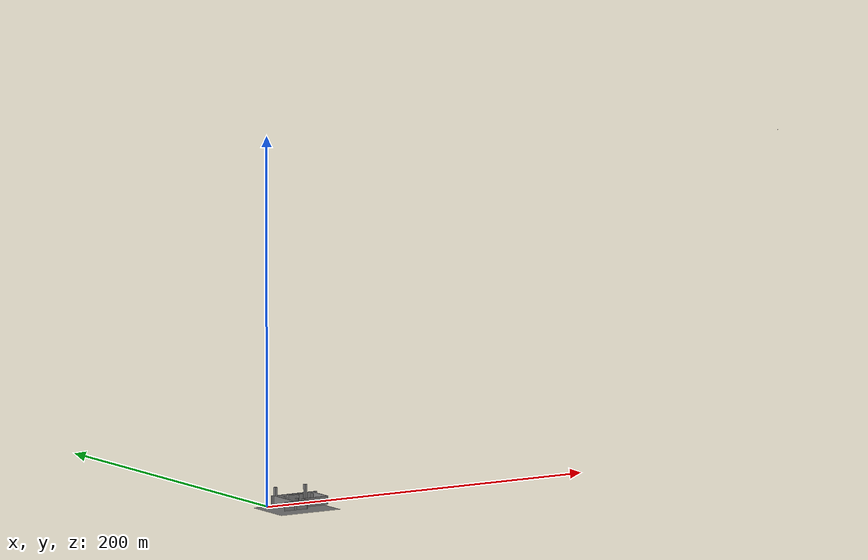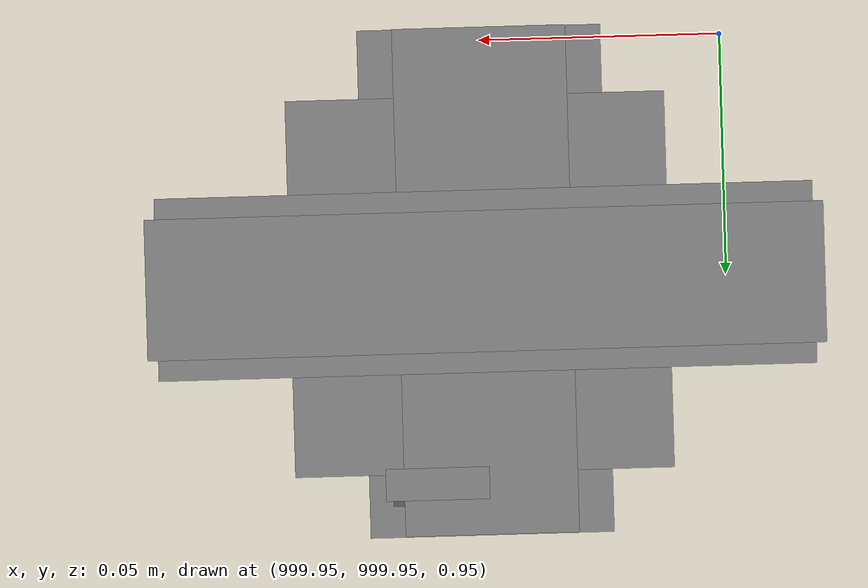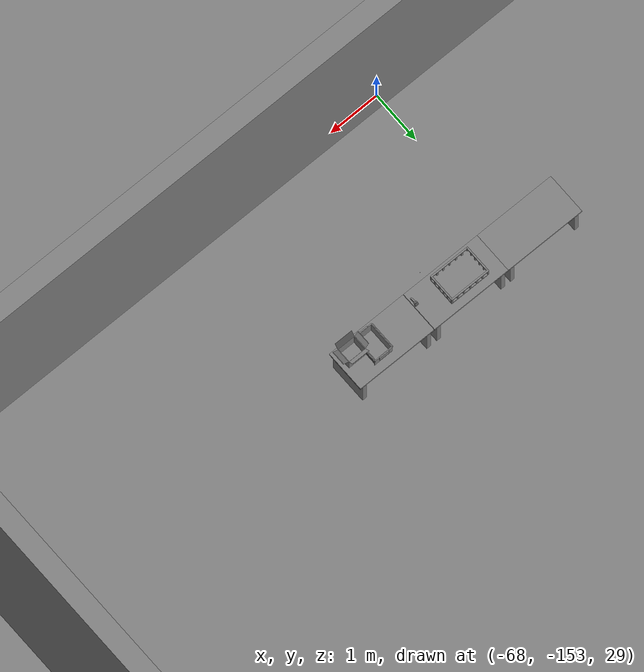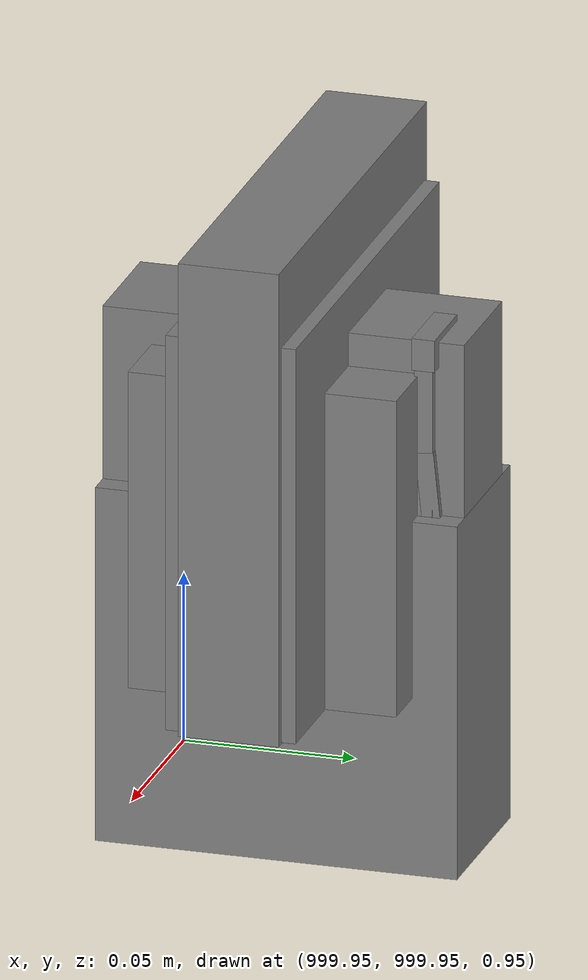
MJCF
<mujoco>
    <option gravity="0.000000000 0.000000000 -9.810000420" timestep="0.0049999999" integrator="implicitfast" density="1.225" viscosity="1.8000001e-05" noslip_iterations="10" iterations="100" sdf_iterations="50">
        <flag multiccd="disable"/>
    </option>
    <size memory="1000M"/>
    <compiler coordinate="local"/>
    <worldbody>
        <light cutoff="30" pos="0 1 1" dir="0 -1 -2"/>
        <light cutoff="30" pos="0 -1 1" dir="0 1 -2"/>
        <body pos="1000.000000000 1000.000000000 1.000000000" euler="0.000000000 0.000000000 180.000000000" name="openloong_gripper_2f85_fix_base_usda_wifi_box">
            <geom contype="1" conaffinity="1" density="1000" type="box" material="" rgba="0.500000000 0.500000000 0.500000000 1.000000000" solimp="0.899999976 0.949999988 0.001000000" friction="1.000000000 0.005000000 0.000100000" solref="0.020000000 1.000000000" margin="0" condim="3" group="0" pos="0.000000000 0.000000000 0.058978677" quat="0.000000000 0.000000047 0.000000000 1.000000000" size="0.068499997 0.018999999 0.059000000" name="openloong_gripper_2f85_fix_base_usda_geom_80F13219_9528_4851_B135_FA7B80A499F4"/>
            <freejoint name="openloong_gripper_2f85_fix_base_usda_wifi_box_joint"/>
            <site size="0.005000000 0.005000000 0.005000000" rgba="0.500000000 0.500000000 0.500000000 1.000000000" pos="0.000000000 0.000000000 0.000000000" quat="0.999961913 0.008726500 0.000000000 0.000000000" group="0" type="sphere" name="openloong_gripper_2f85_fix_base_usda_wifi_boxsite"/>
        </body>
        <body pos="-65.903213501 -149.017929077 31.169446945" euler="166.653762817 -68.070480347 -83.287513733" mocap="true" name="spotlight6_SpotLight"/>
        <body pos="1000.000000000 1000.000000000 1.000000000" euler="0.000000000 0.000000000 180.000000000" name="openloong_gripper_2f85_fix_base_usda_cpu_fan">
            <geom contype="1" conaffinity="1" density="1000" type="box" material="" rgba="0.500000000 0.500000000 0.500000000 1.000000000" solimp="0.899999976 0.949999988 0.001000000" friction="1.000000000 0.005000000 0.000100000" solref="0.020000000 1.000000000" margin="0" condim="3" group="0" pos="0.000000000 0.000000000 0.070034981" quat="0.000000000 0.000000000 0.000000000 1.000000000" size="0.070700005 0.014699999 0.070700005" name="openloong_gripper_2f85_fix_base_usda_geom_A20951FC_5373_47EF_8B19_6EB5347AB32C"/>
            <freejoint name="openloong_gripper_2f85_fix_base_usda_cpu_fan_joint"/>
            <site size="0.005000000 0.005000000 0.005000000" rgba="0.500000000 0.500000000 0.500000000 1.000000000" pos="0.000000000 0.000000000 0.000000000" quat="0.999961913 0.008726535 0.000000000 0.000000000" group="0" type="sphere" name="openloong_gripper_2f85_fix_base_usda_cpu_fancsite"/>
        </body>
        <body pos="1000.000000000 1000.000000000 1.000000000" euler="0.000011953 0.000005123 -179.999984741" name="openloong_gripper_2f85_fix_base_usda_intel_box">
            <geom contype="1" conaffinity="1" density="1000" type="box" material="" rgba="0.500000000 0.500000000 0.500000000 1.000000000" solimp="0.899999976 0.949999988 0.001000000" friction="1.000000000 0.005000000 0.000100000" solref="0.020000000 1.000000000" margin="0" condim="3" group="0" pos="0.000000000 -0.000067139 0.000082284" quat="0.707106709 0.000000225 0.000000253 0.707106650" size="0.052800003 0.025300000 0.052800003" name="openloong_gripper_2f85_fix_base_usda_geom_9881D4BC_01F5_40D0_873C_4B41477560B0"/>
            <freejoint name="openloong_gripper_2f85_fix_base_usda_intel_box_joint"/>
            <site size="0.005000000 0.005000000 0.005000000" rgba="0.500000000 0.500000000 0.500000000 1.000000000" pos="0.000000000 0.000000000 0.000000000" quat="0.999961913 0.008726500 0.000000000 0.000000000" group="0" type="sphere" name="openloong_gripper_2f85_fix_base_usda_intel_boxsite"/>
        </body>
        <body pos="1000.000000000 999.999938965 1.000000000" euler="0.000000000 0.000000000 180.000000000" name="openloong_gripper_2f85_fix_base_usda_intelcore_i5">
            <geom contype="1" conaffinity="1" density="1000" type="box" material="" rgba="0.500000000 0.500000000 0.500000000 1.000000000" solimp="0.899999976 0.949999988 0.001000000" friction="1.000000000 0.005000000 0.000100000" solref="0.020000000 1.000000000" margin="0" condim="3" group="0" pos="0.000000000 0.000000000 0.051722717" quat="0.707106709 0.000000000 0.000000000 -0.707106769" size="0.052800000 0.018080002 0.052800000" name="openloong_gripper_2f85_fix_base_usda_geom_F6A90C24_A447_447C_8CF2_DC80BD13581F"/>
            <freejoint name="openloong_gripper_2f85_fix_base_usda_intelcore_i5_joint"/>
            <site size="0.005000000 0.005000000 0.005000000" rgba="0.500000000 0.500000000 0.500000000 1.000000000" pos="0.000000000 0.000000000 0.000000000" quat="0.999961913 0.008726534 0.000000000 0.000000000" group="0" type="sphere" name="openloong_gripper_2f85_fix_base_usda_intelcore_i5site"/>
        </body>
        <body pos="-66.098510742 -149.533523560 31.167278290" euler="-88.042442322 -3.466108799 26.998922348" mocap="true" name="spotlight1_SpotLight"/>
        <body pos="1000.000000000 1000.000000000 1.000000000" euler="0.000000000 0.000000000 180.000000000" name="openloong_gripper_2f85_fix_base_usda_battery_01">
            <geom contype="1" conaffinity="1" density="1000" type="box" material="" rgba="0.500000000 0.500000000 0.500000000 1.000000000" solimp="0.899999976 0.949999988 0.001000000" friction="1.000000000 0.005000000 0.000100000" solref="0.020000000 1.000000000" margin="0" condim="3" group="0" pos="-0.011123657 -0.041940309 0.101691343" quat="1.000000000 0.000000000 0.000000000 0.000000000" size="0.010800000 0.003375000 0.004725000" name="openloong_gripper_2f85_fix_base_usda_geom_DA64165F_870A_48E2_BB3E_02889FA8B0A4"/>
            <geom contype="1" conaffinity="1" density="1000" type="box" material="" rgba="0.500000000 0.500000000 0.500000000 1.000000000" solimp="0.899999976 0.949999988 0.001000000" friction="1.000000000 0.005000000 0.000100000" solref="0.020000000 1.000000000" margin="0" condim="3" group="0" pos="-0.010876465 -0.044247437 0.047066893" quat="0.998702705 -0.050920475 0.000000000 0.000000000" size="0.009450001 0.002700000 0.024975000" name="openloong_gripper_2f85_fix_base_usda_geom_7FAF71FF_3337_44F8_8FAD_71870D31F394"/>
            <geom contype="1" conaffinity="1" density="1000" type="box" material="" rgba="0.500000000 0.500000000 0.500000000 1.000000000" solimp="0.899999976 0.949999988 0.001000000" friction="1.000000000 0.005000000 0.000100000" solref="0.020000000 1.000000000" margin="0" condim="3" group="0" pos="-0.001235962 -0.000659180 0.047381196" quat="1.000000000 0.000000000 0.000000000 0.000000000" size="0.039420001 0.039150000 0.047250003" name="openloong_gripper_2f85_fix_base_usda_geom_9F033FF6_2753_4B16_9450_982055745EEF"/>
            <geom contype="1" conaffinity="1" density="1000" type="box" material="" rgba="0.500000000 0.500000000 0.500000000 1.000000000" solimp="0.899999976 0.949999988 0.001000000" friction="1.000000000 0.005000000 0.000100000" solref="0.020000000 1.000000000" margin="0" condim="3" group="0" pos="-0.010876465 -0.039138794 0.009851727" quat="1.000000000 0.000000000 0.000000000 0.000000000" size="0.009450001 0.010800000 0.013500000" name="openloong_gripper_2f85_fix_base_usda_geom_687387FD_505D_41DB_852F_B4A7B390748B"/>
            <geom contype="1" conaffinity="1" density="1000" type="box" material="" rgba="0.500000000 0.500000000 0.500000000 1.000000000" solimp="0.899999976 0.949999988 0.001000000" friction="1.000000000 0.005000000 0.000100000" solref="0.020000000 1.000000000" margin="0" condim="3" group="0" pos="-0.010876465 -0.041528322 0.071508206" quat="1.000000000 0.000000000 0.000000000 0.000000000" size="0.009450001 0.002700000 0.027000001" name="openloong_gripper_2f85_fix_base_usda_geom_374D96AF_2A3C_4830_9950_2DD614C52C99"/>
            <freejoint name="openloong_gripper_2f85_fix_base_usda_battery_01_joint"/>
            <site size="0.005000000 0.005000000 0.005000000" rgba="0.500000000 0.500000000 0.500000000 1.000000000" pos="0.000000000 0.000000000 0.000000000" quat="0.999961913 0.008726500 0.000000000 0.000000000" group="0" type="sphere" name="openloong_gripper_2f85_fix_base_usda_battery_01site"/>
        </body>
        <body pos="-66.057670593 -149.135681152 31.166118622" euler="-51.386932373 -67.050827026 128.526229858" mocap="true" name="spotlight4_SpotLight"/>
        <body pos="-64.866622925 -149.383972168 30.183746338" euler="89.999984741 89.999946594 0.000000000" name="openloong_gripper_2f85_fix_base_usda_bluebox_01">
            <geom contype="1" conaffinity="1" density="1000" type="box" material="" rgba="0.500000000 0.500000000 0.500000000 1.000000000" solimp="0.899999976 0.949999988 0.001000000" friction="1.000000000 0.005000000 0.000100000" solref="0.020000000 1.000000000" margin="0" condim="3" group="0" pos="0.276580811 0.187225342 0.000068665" quat="0.707106948 0.000077471 0.707106352 0.000077486" size="0.100000001 0.057999998 0.010000000" name="openloong_gripper_2f85_fix_base_usda_geom_D85EE427_ADFB_457C_8509_0BA68DF05E31"/>
            <geom contype="1" conaffinity="1" density="1000" type="box" material="" rgba="0.500000000 0.500000000 0.500000000 1.000000000" solimp="0.899999976 0.949999988 0.001000000" friction="1.000000000 0.005000000 0.000100000" solref="0.020000000 1.000000000" margin="0" condim="3" group="0" pos="0.000000000 0.002883911 0.000000000" quat="0.999999881 0.000000000 0.000000000 0.000000000" size="0.254000008 0.003000000 0.172000006" name="openloong_gripper_2f85_fix_base_usda_geom_0F0B3BB5_A80F_4197_A62E_8565B589AEB3"/>
            <geom contype="1" conaffinity="1" density="1000" type="box" material="" rgba="0.500000000 0.500000000 0.500000000 1.000000000" solimp="0.899999976 0.949999988 0.001000000" friction="1.000000000 0.005000000 0.000100000" solref="0.020000000 1.000000000" margin="0" condim="3" group="0" pos="0.000000000 0.124874115 0.173484802" quat="0.999796331 0.020176515 -0.000000015 0.000000030" size="0.259999990 0.119999997 0.007000000" name="openloong_gripper_2f85_fix_base_usda_geom_FC3829B4_D1CF_497D_8B34_A230760D5DA8"/>
            <geom contype="1" conaffinity="1" density="1000" type="box" material="" rgba="0.500000000 0.500000000 0.500000000 1.000000000" solimp="0.899999976 0.949999988 0.001000000" friction="1.000000000 0.005000000 0.000100000" solref="0.020000000 1.000000000" margin="0" condim="3" group="0" pos="0.000000000 0.124874115 -0.173469543" quat="0.999796331 -0.020176545 -0.000000015 0.000000000" size="0.259999990 0.119999997 0.007000000" name="openloong_gripper_2f85_fix_base_usda_geom_36F56C51_352A_45B8_9FB6_CE0415500567"/>
            <geom contype="1" conaffinity="1" density="1000" type="box" material="" rgba="0.500000000 0.500000000 0.500000000 1.000000000" solimp="0.899999976 0.949999988 0.001000000" friction="1.000000000 0.005000000 0.000100000" solref="0.020000000 1.000000000" margin="0" condim="3" group="0" pos="0.000000000 0.214008331 0.188980103" quat="0.999912977 0.013176724 0.000000015 0.000000000" size="0.259999990 0.029999999 0.012500000" name="openloong_gripper_2f85_fix_base_usda_geom_0C025837_DB4A_4523_8481_25B1222C3D1B"/>
            <geom contype="1" conaffinity="1" density="1000" type="box" material="" rgba="0.500000000 0.500000000 0.500000000 1.000000000" solimp="0.899999976 0.949999988 0.001000000" friction="1.000000000 0.005000000 0.000100000" solref="0.020000000 1.000000000" margin="0" condim="3" group="0" pos="-0.258361816 0.125289917 0.001876831" quat="0.702796936 -0.020792112 0.710783124 0.020769298" size="0.189999998 0.119999997 0.009000000" name="openloong_gripper_2f85_fix_base_usda_geom_8F7DD63F_9557_4CC0_9DD6_CB3A13C41BD9"/>
            <geom contype="1" conaffinity="1" density="1000" type="box" material="" rgba="0.500000000 0.500000000 0.500000000 1.000000000" solimp="0.899999976 0.949999988 0.001000000" friction="1.000000000 0.005000000 0.000100000" solref="0.020000000 1.000000000" margin="0" condim="3" group="0" pos="0.000000000 0.214008331 -0.188980103" quat="0.999912977 -0.013176769 0.000000030 0.000000015" size="0.259999990 0.029999999 0.012500000" name="openloong_gripper_2f85_fix_base_usda_geom_C686D505_ED31_4E0A_889E_08F3A79224E2"/>
            <geom contype="1" conaffinity="1" density="1000" type="box" material="" rgba="0.500000000 0.500000000 0.500000000 1.000000000" solimp="0.899999976 0.949999988 0.001000000" friction="1.000000000 0.005000000 0.000100000" solref="0.020000000 1.000000000" margin="0" condim="3" group="0" pos="-0.276611328 0.187225342 0.000068665" quat="0.707106650 0.000077441 0.707106709 0.000077456" size="0.100000001 0.057999998 0.010000000" name="openloong_gripper_2f85_fix_base_usda_geom_030FE0CD_A47A_4C28_8F73_7E5F7B524148"/>
            <geom contype="1" conaffinity="1" density="1000" type="box" material="" rgba="0.500000000 0.500000000 0.500000000 1.000000000" solimp="0.899999976 0.949999988 0.001000000" friction="1.000000000 0.005000000 0.000100000" solref="0.020000000 1.000000000" margin="0" condim="3" group="0" pos="0.258331299 0.125289917 0.001876831" quat="0.702851415 0.018856421 0.710823774 -0.019329369" size="0.189999998 0.119999997 0.009000000" name="openloong_gripper_2f85_fix_base_usda_geom_622FE65A_13D1_4B3F_B16A_694A36A50F81"/>
            <freejoint name="openloong_gripper_2f85_fix_base_usda_bluebox_01_joint"/>
            <site size="0.005000000 0.005000000 0.005000000" rgba="0.500000000 0.500000000 0.500000000 1.000000000" pos="0.000000000 0.000000000 0.000000000" quat="0.999961913 0.008726534 0.000000000 0.000000000" group="0" type="sphere" name="openloong_gripper_2f85_fix_base_usda_bluebox_01site"/>
        </body>
        <body pos="-64.496299744 -149.491867065 30.235729218" euler="0.000000000 0.000000000 89.999946594" name="openloong_gripper_2f85_fix_base_usda_cardboardbox_01">
            <geom contype="1" conaffinity="1" density="1000" type="box" material="" rgba="0.500000000 0.500000000 0.500000000 1.000000000" solimp="0.899999976 0.949999988 0.001000000" friction="1.000000000 0.005000000 0.000100000" solref="0.020000000 1.000000000" margin="0" condim="3" group="0" pos="-0.003166199 -0.004086494 0.005052090" quat="1.000000000 0.000000000 0.000000000 0.000000000" size="0.142499998 0.177500010 0.005000000" name="openloong_gripper_2f85_fix_base_usda_geom_769F3BA6_344C_41FD_BA18_9866495A33DF"/>
            <geom contype="1" conaffinity="1" density="1000" type="box" material="" rgba="0.500000000 0.500000000 0.500000000 1.000000000" solimp="0.899999976 0.949999988 0.001000000" friction="1.000000000 0.005000000 0.000100000" solref="0.020000000 1.000000000" margin="0" condim="3" group="0" pos="-0.003166199 0.170316696 0.150570869" quat="1.000000000 0.000000000 0.000000000 0.000000000" size="0.142499998 0.005000000 0.149999991" name="openloong_gripper_2f85_fix_base_usda_geom_C2192AD7_C3BE_49B3_AEB9_806A3A311ECF"/>
            <geom contype="1" conaffinity="1" density="1000" type="box" material="" rgba="0.500000000 0.500000000 0.500000000 1.000000000" solimp="0.899999976 0.949999988 0.001000000" friction="1.000000000 0.005000000 0.000100000" solref="0.020000000 1.000000000" margin="0" condim="3" group="0" pos="-0.147399902 -0.005307198 0.150570869" quat="1.000000000 0.000000000 0.000000000 0.000000000" size="0.005000000 0.177500010 0.149999991" name="openloong_gripper_2f85_fix_base_usda_geom_C6CA8E19_9AB2_45E6_B9D6_3EDE9AFE7FAF"/>
            <geom contype="1" conaffinity="1" density="1000" type="box" material="" rgba="0.500000000 0.500000000 0.500000000 1.000000000" solimp="0.899999976 0.949999988 0.001000000" friction="1.000000000 0.005000000 0.000100000" solref="0.020000000 1.000000000" margin="0" condim="3" group="0" pos="0.140275955 -0.005307198 0.150570869" quat="1.000000000 0.000000000 0.000000000 0.000000000" size="0.005000000 0.177500010 0.149999991" name="openloong_gripper_2f85_fix_base_usda_geom_43BFE710_633D_4B29_937D_A52A4E265EFD"/>
            <geom contype="1" conaffinity="1" density="1000" type="box" material="" rgba="0.500000000 0.500000000 0.500000000 1.000000000" solimp="0.899999976 0.949999988 0.001000000" friction="1.000000000 0.005000000 0.000100000" solref="0.020000000 1.000000000" margin="0" condim="3" group="0" pos="-0.003166199 -0.181550980 0.150570869" quat="1.000000000 0.000000000 0.000000000 0.000000000" size="0.142499998 0.005000000 0.149999991" name="openloong_gripper_2f85_fix_base_usda_geom_A50B2AF2_29C4_4577_90EA_9E41A97AFDFA"/>
            <freejoint name="openloong_gripper_2f85_fix_base_usda_cardboardbox_01_joint"/>
            <site size="0.005000000 0.005000000 0.005000000" rgba="0.500000000 0.500000000 0.500000000 1.000000000" pos="0.000000000 0.000000000 0.000000000" quat="0.999961913 0.008726535 0.000000000 0.000000000" group="0" type="sphere" name="openloong_gripper_2f85_fix_base_usda_site_9D55B09F_3B68_4C42_ACE7_B258767DF1DA"/>
            <body pos="0.139160156 -0.004048347 0.301930904" euler="-179.999954224 49.383502960 179.999954224" name="openloong_gripper_2f85_fix_base_usda_A1_006">
                <geom contype="1" conaffinity="1" density="1000" type="box" material="" rgba="0.500000000 0.500000000 0.500000000 1.000000000" solimp="0.899999976 0.949999988 0.001000000" friction="1.000000000 0.005000000 0.000100000" solref="0.020000000 1.000000000" margin="0" condim="3" group="0" pos="-0.071587563 0.000009537 0.001745224" quat="0.999999881 0.000000000 0.000000000 0.000000000" size="0.071249999 0.179999992 0.002500000" name="openloong_gripper_2f85_fix_base_usda_geom_F9D240A9_DA6F_4639_8A3C_CC786A9E6F3B"/>
                <joint armature="0" stiffness="0.07" damping="0.0099999998" axis="0.000000 1.000000 0.000000" type="hinge" name="openloong_gripper_2f85_fix_base_usda_A1_006"/>
            </body>
            <body pos="-0.145902634 -0.004086494 0.301938057" euler="-180.000000000 -60.000011444 -180.000000000" name="openloong_gripper_2f85_fix_base_usda_A2_006">
                <geom contype="1" conaffinity="1" density="1000" type="box" material="" rgba="0.500000000 0.500000000 0.500000000 1.000000000" solimp="0.899999976 0.949999988 0.001000000" friction="1.000000000 0.005000000 0.000100000" solref="0.020000000 1.000000000" margin="0" condim="3" group="0" pos="0.071268082 0.000009537 0.002717972" quat="0.000002921 0.000000000 -0.000000030 0.999999881" size="0.071249999 0.179999992 0.002500000" name="openloong_gripper_2f85_fix_base_usda_geom_165E6B7A_7EC6_4ADC_B017_ADA184C7D99E"/>
                <joint armature="0" stiffness="0.07" damping="0.0099999998" axis="0.000000 1.000000 0.000000" type="hinge" name="openloong_gripper_2f85_fix_base_usda_A2_006"/>
            </body>
            <body pos="-0.003385544 0.175991058 0.301930904" euler="-125.858116150 -0.000004561 0.000002331" name="openloong_gripper_2f85_fix_base_usda_B2_006">
                <geom contype="1" conaffinity="1" density="1000" type="box" material="" rgba="0.500000000 0.500000000 0.500000000 1.000000000" solimp="0.899999976 0.949999988 0.001000000" friction="1.000000000 0.005000000 0.000100000" solref="0.020000000 1.000000000" margin="0" condim="3" group="0" pos="0.000009537 -0.070939064 -0.002470016" quat="0.999614120 0.027776197 -0.000000015 0.000000030" size="0.137500003 0.064999998 0.005000000" name="openloong_gripper_2f85_fix_base_usda_geom_9025F6E4_BD09_4001_AF56_80D5426020C1"/>
                <joint armature="0" stiffness="0.07" damping="0.0099999998" axis="1.000000 0.000000 0.000000" type="hinge" name="openloong_gripper_2f85_fix_base_usda_B2_006"/>
            </body>
            <body pos="-0.003385544 -0.184140205 0.301938057" euler="147.805557251 0.000000000 0.000000000" name="openloong_gripper_2f85_fix_base_usda_B1_006">
                <geom contype="1" conaffinity="1" density="1000" type="box" material="" rgba="0.500000000 0.500000000 0.500000000 1.000000000" solimp="0.899999976 0.949999988 0.001000000" friction="1.000000000 0.005000000 0.000100000" solref="0.020000000 1.000000000" margin="0" condim="3" group="0" pos="-0.000028610 0.070202351 -0.002703667" quat="0.999614179 -0.027776167 0.000000000 0.000000000" size="0.137500003 0.064999998 0.005000000" name="openloong_gripper_2f85_fix_base_usda_geom_2C274DC2_1A50_4B78_8E94_8210D2F99E13"/>
                <joint armature="0" stiffness="0.07" damping="0.0099999998" axis="1.000000 0.000000 0.000000" type="hinge" name="openloong_gripper_2f85_fix_base_usda_B1_006"/>
            </body>
        </body>
        <body pos="-65.882858276 -149.481979370 30.229999542" euler="-64.487716675 0.000000000 0.000000000" name="openloong_gripper_2f85_fix_base_usda_Barcode">
            <geom contype="1" conaffinity="1" density="1000" type="box" material="" rgba="0.500000000 0.500000000 0.500000000 1.000000000" solimp="0.899999976 0.949999988 0.001000000" friction="1.000000000 0.005000000 0.000100000" solref="0.020000000 1.000000000" margin="0" condim="3" group="0" pos="0.000000000 0.013038635 0.001419067" quat="0.000000000 0.000000000 0.000000000 1.000000119" size="0.034000002 0.010000000 0.017999999" name="openloong_gripper_2f85_fix_base_usda_geom_3FACCD9E_21C5_4890_B67D_CC3BBADFA971"/>
            <geom contype="1" conaffinity="1" density="1000" type="box" material="" rgba="0.500000000 0.500000000 0.500000000 1.000000000" solimp="0.899999976 0.949999988 0.001000000" friction="1.000000000 0.005000000 0.000100000" solref="0.020000000 1.000000000" margin="0" condim="3" group="0" pos="0.000000000 -0.035301208 -0.007095337" quat="0.000000000 0.000000000 -0.043619365 0.999048233" size="0.028999999 0.010000000 0.020000000" name="openloong_gripper_2f85_fix_base_usda_geom_B65FEFCB_2CED_4058_8808_212C6F3F9DDE"/>
            <geom contype="1" conaffinity="1" density="1000" type="box" material="" rgba="0.500000000 0.500000000 0.500000000 1.000000000" solimp="0.899999976 0.949999988 0.001000000" friction="1.000000000 0.005000000 0.000100000" solref="0.020000000 1.000000000" margin="0" condim="3" group="0" pos="0.000000000 -0.043411255 -0.011749268" quat="0.922262907 0.386563420 0.000000000 0.000000000" size="0.026000001 0.010000000 0.020000000" name="openloong_gripper_2f85_fix_base_usda_geom_8DADF931_BF5A_4A3E_BE2A_988BF4898B39"/>
            <geom contype="1" conaffinity="1" density="1000" type="box" material="" rgba="0.500000000 0.500000000 0.500000000 1.000000000" solimp="0.899999976 0.949999988 0.001000000" friction="1.000000000 0.005000000 0.000100000" solref="0.020000000 1.000000000" margin="0" condim="3" group="0" pos="0.000000000 -0.016967773 -0.031860352" quat="0.000000000 0.000000000 0.000000000 1.000000119" size="0.008000000 0.010000000 0.013000000" name="openloong_gripper_2f85_fix_base_usda_geom_39704AB6_82A5_46E0_94E1_E4B1FC5A0428"/>
            <geom contype="1" conaffinity="1" density="1000" type="box" material="" rgba="0.500000000 0.500000000 0.500000000 1.000000000" solimp="0.899999976 0.949999988 0.001000000" friction="1.000000000 0.005000000 0.000100000" solref="0.020000000 1.000000000" margin="0" condim="3" group="0" pos="0.000000000 -0.001869202 0.000312805" quat="0.953716993 0.300705761 0.000000000 0.000000000" size="0.032000002 0.010000000 0.018999999" name="openloong_gripper_2f85_fix_base_usda_geom_62A81445_7AA6_4EF9_AEE7_6D7E30855791"/>
            <geom contype="1" conaffinity="1" density="1000" type="box" material="" rgba="0.500000000 0.500000000 0.500000000 1.000000000" solimp="0.899999976 0.949999988 0.001000000" friction="1.000000000 0.005000000 0.000100000" solref="0.020000000 1.000000000" margin="0" condim="3" group="0" pos="0.000000000 -0.019531250 -0.003173828" quat="0.953716993 0.300705761 0.000000000 0.000000000" size="0.030999999 0.010000000 0.020000000" name="openloong_gripper_2f85_fix_base_usda_geom_9C514FB8_3CDB_4A75_92A4_FB216159C0D3"/>
            <geom contype="1" conaffinity="1" density="1000" type="box" material="" rgba="0.500000000 0.500000000 0.500000000 1.000000000" solimp="0.899999976 0.949999988 0.001000000" friction="1.000000000 0.005000000 0.000100000" solref="0.020000000 1.000000000" margin="0" condim="3" group="0" pos="0.000000000 -0.035301208 -0.007095337" quat="0.953716993 0.300705761 0.000000000 0.000000000" size="0.028999999 0.010000000 0.020000000" name="openloong_gripper_2f85_fix_base_usda_geom_F64A333C_E23C_40D2_BD4C_343C91CEBFFB"/>
            <geom contype="1" conaffinity="1" density="1000" type="box" material="" rgba="0.500000000 0.500000000 0.500000000 1.000000000" solimp="0.899999976 0.949999988 0.001000000" friction="1.000000000 0.005000000 0.000100000" solref="0.020000000 1.000000000" margin="0" condim="3" group="0" pos="0.000000000 -0.042617798 -0.071121216" quat="0.000000000 0.000000000 0.000000000 1.000000119" size="0.013000000 0.021000000 0.059999999" name="openloong_gripper_2f85_fix_base_usda_geom_B8751BD5_1978_4135_95B5_B7815B293371"/>
            <freejoint name="openloong_gripper_2f85_fix_base_usda_Barcode_joint"/>
            <site size="0.005000000 0.005000000 0.005000000" rgba="0.500000000 0.500000000 0.500000000 1.000000000" pos="0.000000000 0.000000000 0.000000000" quat="1.000000000 0.000000000 0.000000000 0.000000000" group="0" type="sphere" name="openloong_gripper_2f85_fix_base_usda_Barcode_site"/>
        </body>
        <body pos="-66.745018005 -149.392349243 30.184000015" euler="0.000000000 0.000000000 89.999946594" name="[22333586217066]_Basket_01">
            <geom contype="1" conaffinity="1" density="1000" type="box" material="" rgba="0.500000000 0.500000000 0.500000000 1.000000000" solimp="0.899999976 0.949999988 0.001000000" friction="1.000000000 0.005000000 0.000100000" solref="0.020000000 1.000000000" margin="0" condim="3" group="0" pos="-0.052425385 0.389207840 0.089787483" quat="0.707107008 0.000000000 0.000000000 0.707106411" size="0.014249999 0.014249999 0.059999999" name="[22333586217066]_geom_F05C6772_C6C6_4E1D_8CC5_C49ACF26FE01"/>
            <geom contype="1" conaffinity="1" density="1000" type="box" material="" rgba="0.500000000 0.500000000 0.500000000 1.000000000" solimp="0.899999976 0.949999988 0.001000000" friction="1.000000000 0.005000000 0.000100000" solref="0.020000000 1.000000000" margin="0" condim="3" group="0" pos="0.264015198 -0.133043289 0.089787483" quat="0.707107008 0.000000000 0.000000000 0.707106411" size="0.014249999 0.014249999 0.059999999" name="[22333586217066]_geom_18C5E934_4097_4C3A_BBBA_8676280BBFE7"/>
            <geom contype="1" conaffinity="1" density="1000" type="box" material="" rgba="0.500000000 0.500000000 0.500000000 1.000000000" solimp="0.899999976 0.949999988 0.001000000" friction="1.000000000 0.005000000 0.000100000" solref="0.020000000 1.000000000" margin="0" condim="3" group="0" pos="-0.264015198 -0.265548706 0.089793205" quat="0.707107008 0.000000000 0.000000000 0.707106411" size="0.014249999 0.014249999 0.059999999" name="[22333586217066]_geom_8DDFDDFD_289A_4EAF_B19A_00E74CCE0A86"/>
            <geom contype="1" conaffinity="1" density="1000" type="box" material="" rgba="0.500000000 0.500000000 0.500000000 1.000000000" solimp="0.899999976 0.949999988 0.001000000" friction="1.000000000 0.005000000 0.000100000" solref="0.020000000 1.000000000" margin="0" condim="3" group="0" pos="-0.160263062 -0.389322281 0.089793205" quat="0.707107008 0.000000000 0.000000000 0.707106411" size="0.014249999 0.014249999 0.059999999" name="[22333586217066]_geom_F2944106_5178_499D_9EAB_DD90A74D7995"/>
            <geom contype="1" conaffinity="1" density="1000" type="box" material="" rgba="0.500000000 0.500000000 0.500000000 1.000000000" solimp="0.899999976 0.949999988 0.001000000" friction="1.000000000 0.005000000 0.000100000" solref="0.020000000 1.000000000" margin="0" condim="3" group="0" pos="0.162265778 -0.389322281 0.089787483" quat="0.707107008 0.000000000 0.000000000 0.707106411" size="0.014249999 0.014249999 0.059999999" name="[22333586217066]_geom_B0386433_7EBD_47B4_A239_E856A7B1EBEE"/>
            <geom contype="1" conaffinity="1" density="1000" type="box" material="" rgba="0.500000000 0.500000000 0.500000000 1.000000000" solimp="0.899999976 0.949999988 0.001000000" friction="1.000000000 0.005000000 0.000100000" solref="0.020000000 1.000000000" margin="0" condim="3" group="0" pos="0.264015198 0.389207840 0.089787483" quat="0.707107008 0.000000000 0.000000000 0.707106411" size="0.014249999 0.014249999 0.059999999" name="[22333586217066]_geom_FF6F914D_0F1C_46AD_8296_D4271C85BA7D"/>
            <geom contype="1" conaffinity="1" density="1000" type="box" material="" rgba="0.500000000 0.500000000 0.500000000 1.000000000" solimp="0.899999976 0.949999988 0.001000000" friction="1.000000000 0.005000000 0.000100000" solref="0.020000000 1.000000000" margin="0" condim="3" group="0" pos="-0.264015198 -0.133043289 0.089793205" quat="0.707107008 0.000000000 0.000000000 0.707106411" size="0.014249999 0.014249999 0.059999999" name="[22333586217066]_geom_2054CD47_69E8_4C6B_AA01_E7635AE0FB38"/>
            <geom contype="1" conaffinity="1" density="1000" type="box" material="" rgba="0.500000000 0.500000000 0.500000000 1.000000000" solimp="0.899999976 0.949999988 0.001000000" friction="1.000000000 0.005000000 0.000100000" solref="0.020000000 1.000000000" margin="0" condim="3" group="0" pos="-0.264026642 0.269256592 0.089793205" quat="0.707107008 0.000000000 0.000000000 0.707106411" size="0.014249999 0.014249999 0.059999999" name="[22333586217066]_geom_57FE0B0D_75C0_4224_B06A_FE799B7A6CBE"/>
            <geom contype="1" conaffinity="1" density="1000" type="box" material="" rgba="0.500000000 0.500000000 0.500000000 1.000000000" solimp="0.899999976 0.949999988 0.001000000" friction="1.000000000 0.005000000 0.000100000" solref="0.020000000 1.000000000" margin="0" condim="3" group="0" pos="0.054462433 0.389207840 0.089787483" quat="0.707107008 0.000000000 0.000000000 0.707106411" size="0.014249999 0.014249999 0.059999999" name="[22333586217066]_geom_8297E166_F698_459F_B39D_B902143C9196"/>
            <geom contype="1" conaffinity="1" density="1000" type="box" material="" rgba="0.500000000 0.500000000 0.500000000 1.000000000" solimp="0.899999976 0.949999988 0.001000000" friction="1.000000000 0.005000000 0.000100000" solref="0.020000000 1.000000000" margin="0" condim="3" group="0" pos="0.054462433 -0.389322281 0.089787483" quat="0.707107008 0.000000000 0.000000000 0.707106411" size="0.014249999 0.014249999 0.059999999" name="[22333586217066]_geom_B985DE9B_AC95_441E_BA30_D9358226E56C"/>
            <geom contype="1" conaffinity="1" density="1000" type="box" material="" rgba="0.500000000 0.500000000 0.500000000 1.000000000" solimp="0.899999976 0.949999988 0.001000000" friction="1.000000000 0.005000000 0.000100000" solref="0.020000000 1.000000000" margin="0" condim="3" group="0" pos="0.264015198 0.269256592 0.089793205" quat="0.707107008 0.000000000 0.000000000 0.707106411" size="0.014249999 0.014249999 0.059999999" name="[22333586217066]_geom_9C83AFBB_D402_4A93_94B0_A5A92E369BD3"/>
            <geom contype="1" conaffinity="1" density="1000" type="box" material="" rgba="0.500000000 0.500000000 0.500000000 1.000000000" solimp="0.899999976 0.949999988 0.001000000" friction="1.000000000 0.005000000 0.000100000" solref="0.020000000 1.000000000" margin="0" condim="3" group="0" pos="0.264015198 -0.389322281 0.089787483" quat="0.707107008 0.000000000 0.000000000 0.707106411" size="0.014249999 0.014249999 0.059999999" name="[22333586217066]_geom_FDD51EFC_2DBB_498D_B0E1_A9079ABF4821"/>
            <geom contype="1" conaffinity="1" density="1000" type="box" material="" rgba="0.500000000 0.500000000 0.500000000 1.000000000" solimp="0.899999976 0.949999988 0.001000000" friction="1.000000000 0.005000000 0.000100000" solref="0.020000000 1.000000000" margin="0" condim="3" group="0" pos="0.000000000 0.000000000 0.015998840" quat="0.707107008 0.000000000 0.000000000 0.707106411" size="0.403499991 0.279000014 0.015750000" name="[22333586217066]_geom_3B2002FC_C572_4978_A52A_6E3F68136B10"/>
            <geom contype="1" conaffinity="1" density="1000" type="box" material="" rgba="0.500000000 0.500000000 0.500000000 1.000000000" solimp="0.899999976 0.949999988 0.001000000" friction="1.000000000 0.005000000 0.000100000" solref="0.020000000 1.000000000" margin="0" condim="3" group="0" pos="0.000000000 -0.389476776 0.163619041" quat="0.707107008 0.000000000 0.000000000 0.707106411" size="0.015000000 0.277500004 0.015750000" name="[22333586217066]_geom_851BAEA8_3AD3_4676_AE8D_90CD59F9A200"/>
            <geom contype="1" conaffinity="1" density="1000" type="box" material="" rgba="0.500000000 0.500000000 0.500000000 1.000000000" solimp="0.899999976 0.949999988 0.001000000" friction="1.000000000 0.005000000 0.000100000" solref="0.020000000 1.000000000" margin="0" condim="3" group="0" pos="0.162265778 0.389207840 0.089787483" quat="0.707107008 0.000000000 0.000000000 0.707106411" size="0.014249999 0.014249999 0.059999999" name="[22333586217066]_geom_6AE7775A_F0C0_413C_BE67_5FBCCAA37F24"/>
            <geom contype="1" conaffinity="1" density="1000" type="box" material="" rgba="0.500000000 0.500000000 0.500000000 1.000000000" solimp="0.899999976 0.949999988 0.001000000" friction="1.000000000 0.005000000 0.000100000" solref="0.020000000 1.000000000" margin="0" condim="3" group="0" pos="0.000000000 0.389471054 0.163619041" quat="0.707107008 0.000000000 0.000000000 0.707106411" size="0.015000000 0.277500004 0.015750000" name="[22333586217066]_geom_9B6B33D5_7D20_4EEB_A9BC_8D65DEC02263"/>
            <geom contype="1" conaffinity="1" density="1000" type="box" material="" rgba="0.500000000 0.500000000 0.500000000 1.000000000" solimp="0.899999976 0.949999988 0.001000000" friction="1.000000000 0.005000000 0.000100000" solref="0.020000000 1.000000000" margin="0" condim="3" group="0" pos="-0.263511658 0.000000000 0.163619041" quat="0.707107008 0.000000000 0.000000000 0.707106411" size="0.403499991 0.015000000 0.015750000" name="[22333586217066]_geom_ED7D6F8D_A00C_47AB_B1CB_035BFE643D88"/>
            <geom contype="1" conaffinity="1" density="1000" type="box" material="" rgba="0.500000000 0.500000000 0.500000000 1.000000000" solimp="0.899999976 0.949999988 0.001000000" friction="1.000000000 0.005000000 0.000100000" solref="0.020000000 1.000000000" margin="0" condim="3" group="0" pos="-0.264015198 0.141334534 0.089793205" quat="0.707107008 0.000000000 0.000000000 0.707106411" size="0.014249999 0.014249999 0.059999999" name="[22333586217066]_geom_6E3B9AE7_54E9_4AF5_82A4_6CB434DBF367"/>
            <geom contype="1" conaffinity="1" density="1000" type="box" material="" rgba="0.500000000 0.500000000 0.500000000 1.000000000" solimp="0.899999976 0.949999988 0.001000000" friction="1.000000000 0.005000000 0.000100000" solref="0.020000000 1.000000000" margin="0" condim="3" group="0" pos="0.264015198 -0.265548706 0.089787483" quat="0.707107008 0.000000000 0.000000000 0.707106411" size="0.014249999 0.014249999 0.059999999" name="[22333586217066]_geom_F03BB6E0_E70F_44E4_81BA_CAC6F4E5A241"/>
            <geom contype="1" conaffinity="1" density="1000" type="box" material="" rgba="0.500000000 0.500000000 0.500000000 1.000000000" solimp="0.899999976 0.949999988 0.001000000" friction="1.000000000 0.005000000 0.000100000" solref="0.020000000 1.000000000" margin="0" condim="3" group="0" pos="-0.160263062 0.389207840 0.089787483" quat="0.707107008 0.000000000 0.000000000 0.707106411" size="0.014249999 0.014249999 0.059999999" name="[22333586217066]_geom_B7EDFCD6_1B04_45C5_BC9F_47797A118801"/>
            <geom contype="1" conaffinity="1" density="1000" type="box" material="" rgba="0.500000000 0.500000000 0.500000000 1.000000000" solimp="0.899999976 0.949999988 0.001000000" friction="1.000000000 0.005000000 0.000100000" solref="0.020000000 1.000000000" margin="0" condim="3" group="0" pos="-0.052425385 -0.389322281 0.089787483" quat="0.707107008 0.000000000 0.000000000 0.707106411" size="0.014249999 0.014249999 0.059999999" name="[22333586217066]_geom_F9F0CBF1_6EF7_4E90_8FFA_093426E3ABDE"/>
            <geom contype="1" conaffinity="1" density="1000" type="box" material="" rgba="0.500000000 0.500000000 0.500000000 1.000000000" solimp="0.899999976 0.949999988 0.001000000" friction="1.000000000 0.005000000 0.000100000" solref="0.020000000 1.000000000" margin="0" condim="3" group="0" pos="-0.264026642 -0.389322281 0.089793205" quat="0.707107008 0.000000000 0.000000000 0.707106411" size="0.014249999 0.014249999 0.059999999" name="[22333586217066]_geom_873FD26C_0131_4726_9C8D_17282D97AC18"/>
            <geom contype="1" conaffinity="1" density="1000" type="box" material="" rgba="0.500000000 0.500000000 0.500000000 1.000000000" solimp="0.899999976 0.949999988 0.001000000" friction="1.000000000 0.005000000 0.000100000" solref="0.020000000 1.000000000" margin="0" condim="3" group="0" pos="0.264015198 0.141334534 0.089787483" quat="0.707107008 0.000000000 0.000000000 0.707106411" size="0.014249999 0.014249999 0.059999999" name="[22333586217066]_geom_D14DE457_6F3B_46AA_B762_B8F1F5597EB7"/>
            <geom contype="1" conaffinity="1" density="1000" type="box" material="" rgba="0.500000000 0.500000000 0.500000000 1.000000000" solimp="0.899999976 0.949999988 0.001000000" friction="1.000000000 0.005000000 0.000100000" solref="0.020000000 1.000000000" margin="0" condim="3" group="0" pos="-0.264015198 0.389207840 0.089793205" quat="0.707107008 0.000000000 0.000000000 0.707106411" size="0.014249999 0.014249999 0.059999999" name="[22333586217066]_geom_382CEF38_A237_4BF7_8934_319FC8F38E84"/>
            <geom contype="1" conaffinity="1" density="1000" type="box" material="" rgba="0.500000000 0.500000000 0.500000000 1.000000000" solimp="0.899999976 0.949999988 0.001000000" friction="1.000000000 0.005000000 0.000100000" solref="0.020000000 1.000000000" margin="0" condim="3" group="0" pos="0.264015198 0.004480362 0.089787483" quat="0.707107008 0.000000000 0.000000000 0.707106411" size="0.014249999 0.014249999 0.059999999" name="[22333586217066]_geom_AED04D76_1C58_46FC_A57A_D834DC54A5F3"/>
            <geom contype="1" conaffinity="1" density="1000" type="box" material="" rgba="0.500000000 0.500000000 0.500000000 1.000000000" solimp="0.899999976 0.949999988 0.001000000" friction="1.000000000 0.005000000 0.000100000" solref="0.020000000 1.000000000" margin="0" condim="3" group="0" pos="0.263694763 -0.000011444 0.163619041" quat="0.707107008 0.000000000 0.000000000 0.707106411" size="0.403499991 0.015000000 0.015750000" name="[22333586217066]_geom_77123946_418F_4CE2_A07E_6FCFE4E0C28C"/>
            <geom contype="1" conaffinity="1" density="1000" type="box" material="" rgba="0.500000000 0.500000000 0.500000000 1.000000000" solimp="0.899999976 0.949999988 0.001000000" friction="1.000000000 0.005000000 0.000100000" solref="0.020000000 1.000000000" margin="0" condim="3" group="0" pos="-0.264015198 0.004480362 0.089793205" quat="0.707107008 0.000000000 0.000000000 0.707106411" size="0.014249999 0.014249999 0.059999999" name="[22333586217066]_geom_BBD9B6B9_7365_4D9B_94F9_08A0B59BA4E1"/>
            <freejoint name="[22333586217066]_joint_EC113BB4_5E9B_4989_A8B9_E524414A9936"/>
        </body>
        <body pos="0.000000000 0.000000000 0.000000000" euler="0.000000000 0.000000000 0.000000000" name="Static Objects_Static Objects">
            <geom contype="1" conaffinity="1" density="1000" type="box" material="" rgba="0.500000000 0.500000000 0.500000000 1.000000000" solimp="0.899999976 0.949999988 0.001000000" friction="1.000000000 0.005000000 0.000100000" solref="0.020000000 1.000000000" margin="0" condim="3" group="0" pos="-67.544113159 -149.365814209 29.727830887" quat="0.500000417 0.499999970 0.499999553 0.499999970" size="0.381000012 0.319999993 0.041000001" name="Static Objects_geom_93D4C292_0F25_4FFA_A913_A373994428E4"/>
            <geom contype="1" conaffinity="1" density="1000" type="box" material="" rgba="0.500000000 0.500000000 0.500000000 1.000000000" solimp="0.899999976 0.949999988 0.001000000" friction="1.000000000 0.005000000 0.000100000" solref="0.020000000 1.000000000" margin="0" condim="3" group="0" pos="-68.239501953 -149.365814209 30.086868286" quat="0.500000417 0.499999970 0.499999553 0.499999970" size="0.370999992 0.039500002 0.745000005" name="Static Objects_geom_BFDFF61F_54BF_42AA_A482_9DE4483AE674"/>
            <geom contype="1" conaffinity="1" density="1000" type="box" material="" rgba="0.500000000 0.500000000 0.500000000 1.000000000" solimp="0.899999976 0.949999988 0.001000000" friction="1.000000000 0.005000000 0.000100000" solref="0.020000000 1.000000000" margin="0" condim="3" group="0" pos="-68.239501953 -149.365814209 30.147235870" quat="0.500000417 0.499999970 0.499999553 0.499999970" size="0.400000006 0.022000000 0.800000012" name="Static Objects_geom_414B883B_DED8_4B5B_B56D_BD59DF1F80FF"/>
            <geom contype="1" conaffinity="1" density="1000" type="box" material="" rgba="0.500000000 0.500000000 0.500000000 1.000000000" solimp="0.899999976 0.949999988 0.001000000" friction="1.000000000 0.005000000 0.000100000" solref="0.020000000 1.000000000" margin="0" condim="3" group="0" pos="-68.934890747 -149.365814209 29.727830887" quat="0.500000417 0.499999970 0.499999553 0.499999970" size="0.381000012 0.319999993 0.041000001" name="Static Objects_geom_FE760B5A_BFF4_4FA2_BF24_914322FBD7A8"/>
            <geom contype="1" conaffinity="1" density="1000" type="box" material="" rgba="0.500000000 0.500000000 0.500000000 1.000000000" solimp="0.899999976 0.949999988 0.001000000" friction="1.000000000 0.005000000 0.000100000" solref="0.020000000 1.000000000" margin="0" condim="3" group="0" pos="-68.239501953 -149.365814209 29.561563492" quat="0.500000417 0.499999970 0.499999553 0.499999970" size="0.020000000 0.022000000 0.660000026" name="Static Objects_geom_270802F6_6B61_4F52_90FF_046E38EA4FAC"/>
            <geom contype="1" conaffinity="1" density="1000" type="box" material="" rgba="0.500000000 0.500000000 0.500000000 1.000000000" solimp="0.899999976 0.949999988 0.001000000" friction="1.000000000 0.005000000 0.000100000" solref="0.020000000 1.000000000" margin="0" condim="3" group="0" pos="-65.945671082 -149.365814209 29.727830887" quat="0.500000417 0.499999970 0.499999553 0.499999970" size="0.381000012 0.319999993 0.041000001" name="Static Objects_geom_22E83361_CAD1_4923_A49C_2F5CB5F3744F"/>
            <geom contype="1" conaffinity="1" density="1000" type="box" material="" rgba="0.500000000 0.500000000 0.500000000 1.000000000" solimp="0.899999976 0.949999988 0.001000000" friction="1.000000000 0.005000000 0.000100000" solref="0.020000000 1.000000000" margin="0" condim="3" group="0" pos="-66.641059875 -149.365814209 30.086868286" quat="0.500000417 0.499999970 0.499999553 0.499999970" size="0.370999992 0.039500002 0.745000005" name="Static Objects_geom_152D55A5_7F3D_4EBD_8342_71DAE3181841"/>
            <geom contype="1" conaffinity="1" density="1000" type="box" material="" rgba="0.500000000 0.500000000 0.500000000 1.000000000" solimp="0.899999976 0.949999988 0.001000000" friction="1.000000000 0.005000000 0.000100000" solref="0.020000000 1.000000000" margin="0" condim="3" group="0" pos="-66.641059875 -149.365814209 30.147235870" quat="0.500000417 0.499999970 0.499999553 0.499999970" size="0.400000006 0.022000000 0.800000012" name="Static Objects_geom_81B7BFB1_DFDF_4332_ACFA_8027DBC76B28"/>
            <geom contype="1" conaffinity="1" density="1000" type="box" material="" rgba="0.500000000 0.500000000 0.500000000 1.000000000" solimp="0.899999976 0.949999988 0.001000000" friction="1.000000000 0.005000000 0.000100000" solref="0.020000000 1.000000000" margin="0" condim="3" group="0" pos="-67.336448669 -149.365814209 29.727830887" quat="0.500000417 0.499999970 0.499999553 0.499999970" size="0.381000012 0.319999993 0.041000001" name="Static Objects_geom_45CFFBF9_3BCE_4854_9898_A53C48BF3A66"/>
            <geom contype="1" conaffinity="1" density="1000" type="box" material="" rgba="0.500000000 0.500000000 0.500000000 1.000000000" solimp="0.899999976 0.949999988 0.001000000" friction="1.000000000 0.005000000 0.000100000" solref="0.020000000 1.000000000" margin="0" condim="3" group="0" pos="-66.641059875 -149.365814209 29.561563492" quat="0.500000417 0.499999970 0.499999553 0.499999970" size="0.020000000 0.022000000 0.660000026" name="Static Objects_geom_E3FABEC1_A0A4_4AFF_9B5A_81AB10DCB86E"/>
            <geom contype="1" conaffinity="1" density="1000" type="box" material="" rgba="0.500000000 0.500000000 0.500000000 1.000000000" solimp="0.899999976 0.949999988 0.001000000" friction="1.000000000 0.005000000 0.000100000" solref="0.020000000 1.000000000" margin="0" condim="3" group="0" pos="-64.338577271 -149.365814209 29.727830887" quat="0.500000417 0.499999970 0.499999553 0.499999970" size="0.381000012 0.319999993 0.041000001" name="Static Objects_geom_C6E104EA_B92F_4D53_9734_CA196F7F261A"/>
            <geom contype="1" conaffinity="1" density="1000" type="box" material="" rgba="0.500000000 0.500000000 0.500000000 1.000000000" solimp="0.899999976 0.949999988 0.001000000" friction="1.000000000 0.005000000 0.000100000" solref="0.020000000 1.000000000" margin="0" condim="3" group="0" pos="-65.033966064 -149.365814209 30.086868286" quat="0.500000417 0.499999970 0.499999553 0.499999970" size="0.370999992 0.039500002 0.745000005" name="Static Objects_geom_3F5C0136_0DC9_43CA_8838_CBBFB86B0033"/>
            <geom contype="1" conaffinity="1" density="1000" type="box" material="" rgba="0.500000000 0.500000000 0.500000000 1.000000000" solimp="0.899999976 0.949999988 0.001000000" friction="1.000000000 0.005000000 0.000100000" solref="0.020000000 1.000000000" margin="0" condim="3" group="0" pos="-65.033966064 -149.365814209 30.147235870" quat="0.500000417 0.499999970 0.499999553 0.499999970" size="0.400000006 0.022000000 0.800000012" name="Static Objects_geom_B69C59FD_4569_4D14_841C_3EEE1523A45B"/>
            <geom contype="1" conaffinity="1" density="1000" type="box" material="" rgba="0.500000000 0.500000000 0.500000000 1.000000000" solimp="0.899999976 0.949999988 0.001000000" friction="1.000000000 0.005000000 0.000100000" solref="0.020000000 1.000000000" margin="0" condim="3" group="0" pos="-65.729354858 -149.365814209 29.727830887" quat="0.500000417 0.499999970 0.499999553 0.499999970" size="0.381000012 0.319999993 0.041000001" name="Static Objects_geom_5C2687C1_2890_474C_B711_FA24F5E4BF3B"/>
            <geom contype="1" conaffinity="1" density="1000" type="box" material="" rgba="0.500000000 0.500000000 0.500000000 1.000000000" solimp="0.899999976 0.949999988 0.001000000" friction="1.000000000 0.005000000 0.000100000" solref="0.020000000 1.000000000" margin="0" condim="3" group="0" pos="-65.033966064 -149.365814209 29.561563492" quat="0.500000417 0.499999970 0.499999553 0.499999970" size="0.020000000 0.022000000 0.660000026" name="Static Objects_geom_B8DECF04_B97D_473E_9143_0E9676EC3745"/>
            <geom contype="1" conaffinity="1" density="1000" type="box" material="" rgba="0.500000000 0.500000000 0.500000000 1.000000000" solimp="0.899999976 0.949999988 0.001000000" friction="1.000000000 0.005000000 0.000100000" solref="0.020000000 1.000000000" margin="0" condim="3" group="0" pos="-61.754566193 -137.853729248 33.906845093" quat="0.707107067 0.000000000 0.000000000 0.707106471" size="0.759999990 0.759999990 4.500000000" name="Static Objects_geom_ACA596FF_7704_4DD3_BE88_EEEF4A2B918D"/>
            <geom contype="1" conaffinity="1" density="1000" type="box" material="" rgba="0.500000000 0.500000000 0.500000000 1.000000000" solimp="0.899999976 0.949999988 0.001000000" friction="1.000000000 0.005000000 0.000100000" solref="0.020000000 1.000000000" margin="0" condim="3" group="0" pos="-57.511135101 -144.927108765 31.707921982" quat="1.000000000 0.000000000 0.000000000 0.000000000" size="0.200000003 8.000000000 2.299999952" name="Static Objects_geom_354205C2_2489_414D_9D7B_37EAF685E703"/>
            <geom contype="1" conaffinity="1" density="1000" type="box" material="" rgba="0.500000000 0.500000000 0.500000000 1.000000000" solimp="0.899999976 0.949999988 0.001000000" friction="1.000000000 0.005000000 0.000100000" solref="0.020000000 1.000000000" margin="0" condim="3" group="0" pos="-80.517646790 -157.574050903 31.688196182" quat="0.707107067 0.000000000 0.000000000 0.707106471" size="0.600000024 0.600000024 2.299999952" name="Static Objects_geom_70278CB3_28B0_47AC_B9D1_89C2FA5E7F1E"/>
            <geom contype="1" conaffinity="1" density="1000" type="box" material="" rgba="0.500000000 0.500000000 0.500000000 1.000000000" solimp="0.899999976 0.949999988 0.001000000" friction="1.000000000 0.005000000 0.000100000" solref="0.020000000 1.000000000" margin="0" condim="3" group="0" pos="-80.711044312 -147.414932251 31.666158676" quat="1.000000000 0.000000000 0.000000000 0.000000000" size="0.200000003 10.000000000 2.299999952" name="Static Objects_geom_2CC593D0_98A5_4C7C_8793_CD3BC7DFB7FF"/>
            <geom contype="1" conaffinity="1" density="1000" type="box" material="" rgba="0.500000000 0.500000000 0.500000000 1.000000000" solimp="0.899999976 0.949999988 0.001000000" friction="1.000000000 0.005000000 0.000100000" solref="0.020000000 1.000000000" margin="0" condim="3" group="0" pos="-57.687217712 -137.434692383 31.688196182" quat="0.707107067 0.000000000 0.000000000 0.707106471" size="0.600000024 0.600000024 2.299999952" name="Static Objects_geom_BF7EEF83_70FD_4AAB_8E25_690CCDE74282"/>
            <geom contype="1" conaffinity="1" density="1000" type="box" material="" rgba="0.500000000 0.500000000 0.500000000 1.000000000" solimp="0.899999976 0.949999988 0.001000000" friction="1.000000000 0.005000000 0.000100000" solref="0.020000000 1.000000000" margin="0" condim="3" group="0" pos="-69.537033081 -140.263229370 31.714921951" quat="0.707107067 0.000000000 0.000000000 0.707106471" size="0.759999990 4.500000000 2.299999952" name="Static Objects_geom_AEF0DB33_7284_4B9A_9432_DEC20456A9EC"/>
            <geom contype="1" conaffinity="1" density="1000" type="box" material="" rgba="0.500000000 0.500000000 0.500000000 1.000000000" solimp="0.899999976 0.949999988 0.001000000" friction="1.000000000 0.005000000 0.000100000" solref="0.020000000 1.000000000" margin="0" condim="3" group="0" pos="-80.073638916 -137.853713989 33.906845093" quat="0.707107067 0.000000000 0.000000000 0.707106471" size="0.759999990 0.759999990 4.500000000" name="Static Objects_geom_26556D2E_8181_4292_8F8E_365C803008CE"/>
            <geom contype="1" conaffinity="1" density="1000" type="box" material="" rgba="0.500000000 0.500000000 0.500000000 1.000000000" solimp="0.899999976 0.949999988 0.001000000" friction="1.000000000 0.005000000 0.000100000" solref="0.020000000 1.000000000" margin="0" condim="3" group="0" pos="-73.406707764 -155.734664917 31.707921982" quat="1.000000000 0.000000000 0.000000000 0.000000000" size="0.200000003 3.000000000 2.299999952" name="Static Objects_geom_5F46E84D_73E2_4DC6_922F_0A422E3B80F0"/>
            <geom contype="1" conaffinity="1" density="1000" type="box" material="" rgba="0.500000000 0.500000000 0.500000000 1.000000000" solimp="0.899999976 0.949999988 0.001000000" friction="1.000000000 0.005000000 0.000100000" solref="0.020000000 1.000000000" margin="0" condim="3" group="0" pos="-68.497543335 -137.448257446 31.707921982" quat="0.707107067 0.000000000 0.000000000 0.707106471" size="0.200000003 14.000000000 2.299999952" name="Static Objects_geom_489D16A3_2973_4986_98FE_A8071CD090D3"/>
            <geom contype="1" conaffinity="1" density="1000" type="cylinder" material="" rgba="0.500000000 0.500000000 0.500000000 1.000000000" solimp="0.899999976 0.949999988 0.001000000" friction="1.000000000 0.005000000 0.000100000" solref="0.020000000 1.000000000" margin="0" condim="3" group="0" pos="-68.868522644 -142.134506226 31.711090088" quat="0.707107067 0.000000000 0.000000000 0.707106471" size="0.509999990 2.299999952 1.000000000" name="Static Objects_geom_782D76B5_A5CD_444F_A1F7_29FA3372EE03"/>
            <geom contype="1" conaffinity="1" density="1000" type="plane" material="" rgba="0.500000000 0.500000000 0.500000000 1.000000000" solimp="0.899999976 0.949999988 0.001000000" friction="1.000000000 0.005000000 0.000100000" solref="0.020000000 1.000000000" margin="0" condim="3" group="0" pos="-72.873703003 -147.131927490 29.409669876" quat="1.000000000 0.000000000 0.000000000 0.000000000" size="18.000000000 14.000000000 1.000000000" name="Static Objects_geom_2297DC5F_24A5_49BB_B6F6_6941F7166AA7"/>
            <geom contype="1" conaffinity="1" density="1000" type="box" material="" rgba="0.500000000 0.500000000 0.500000000 1.000000000" solimp="0.899999976 0.949999988 0.001000000" friction="1.000000000 0.005000000 0.000100000" solref="0.020000000 1.000000000" margin="0" condim="3" group="0" pos="-79.943580627 -157.782272339 31.707921982" quat="0.707107067 0.000000000 0.000000000 0.707106471" size="0.200000003 7.000000000 2.299999952" name="Static Objects_geom_DE87EC6F_354E_4E54_9FDC_030D601D7CC1"/>
            <geom contype="1" conaffinity="1" density="1000" type="box" material="" rgba="0.500000000 0.500000000 0.500000000 1.000000000" solimp="0.899999976 0.949999988 0.001000000" friction="1.000000000 0.005000000 0.000100000" solref="0.020000000 1.000000000" margin="0" condim="3" group="0" pos="-65.421028137 -152.903442383 31.707921982" quat="0.707107067 0.000000000 0.000000000 0.707106471" size="0.200000003 7.800000191 2.299999952" name="Static Objects_geom_5B69F2FF_0507_46C3_A8D6_BC6315692BB1"/>
            <geom contype="1" conaffinity="1" density="1000" type="box" material="" rgba="0.500000000 0.500000000 0.500000000 1.000000000" solimp="0.899999976 0.949999988 0.001000000" friction="1.000000000 0.005000000 0.000100000" solref="0.020000000 1.000000000" margin="0" condim="3" group="0" pos="-74.776908875 -149.964416504 31.688196182" quat="1.000000000 0.000000000 0.000000000 0.000000000" size="0.600000024 0.409999996 2.299999952" name="Static Objects_geom_2933129D_0B6A_44BB_AA95_6E8A7BD3C3AB"/>
            <geom contype="1" conaffinity="1" density="1000" type="cylinder" material="" rgba="0.500000000 0.500000000 0.500000000 1.000000000" solimp="0.899999976 0.949999988 0.001000000" friction="1.000000000 0.005000000 0.000100000" solref="0.020000000 1.000000000" margin="0" condim="3" group="0" pos="-60.161884308 -142.134506226 31.711090088" quat="0.707107067 0.000000000 0.000000000 0.707106471" size="0.509999990 2.299999952 1.000000000" name="Static Objects_geom_350ABBF4_06DC_4D40_8EB7_454F7434CC97"/>
            <geom contype="1" conaffinity="1" density="1000" type="cylinder" material="" rgba="0.500000000 0.500000000 0.500000000 1.000000000" solimp="0.899999976 0.949999988 0.001000000" friction="1.000000000 0.005000000 0.000100000" solref="0.020000000 1.000000000" margin="0" condim="3" group="0" pos="-75.382453918 -149.963455200 31.711090088" quat="0.707107067 0.000000000 0.000000000 0.707106471" size="0.409999996 2.299999952 1.000000000" name="Static Objects_geom_510C8BE5_4F2C_49DF_8FBF_2EB066F344C8"/>
            <geom contype="1" conaffinity="1" density="1000" type="cylinder" material="" rgba="0.500000000 0.500000000 0.500000000 1.000000000" solimp="0.899999976 0.949999988 0.001000000" friction="1.000000000 0.005000000 0.000100000" solref="0.020000000 1.000000000" margin="0" condim="3" group="0" pos="-74.154960632 -149.963455200 31.711090088" quat="0.707107067 0.000000000 0.000000000 0.707106471" size="0.409999996 2.299999952 1.000000000" name="Static Objects_geom_EE48C92E_A24B_4F1B_9B47_0A2F4FC0166C"/>
            <geom contype="1" conaffinity="1" density="1000" type="cylinder" material="" rgba="0.500000000 0.500000000 0.500000000 1.000000000" solimp="0.899999976 0.949999988 0.001000000" friction="1.000000000 0.005000000 0.000100000" solref="0.020000000 1.000000000" margin="0" condim="3" group="0" pos="-77.566612244 -142.134506226 31.711090088" quat="0.707107067 0.000000000 0.000000000 0.707106471" size="0.509999990 2.299999952 1.000000000" name="Static Objects_geom_05DAE820_2C18_4649_A244_3313EC5D7600"/>
        </body>
        <body pos="-66.291030884 -149.869689941 29.018842697" euler="0.000000000 0.000000000 89.999946594" mocap="true" name="openloong_gripper_2f85_fix_base_usda_leftHandMocap"/>
        <body pos="-66.291030884 -149.869689941 29.018842697" euler="0.000000000 0.000000000 89.999946594" mocap="true" name="openloong_gripper_2f85_fix_base_usda_rightHandMocap"/>
        <body pos="-66.291030884 -149.869689941 30.218843460" euler="0.000000000 0.000000000 89.999946594" name="openloong_gripper_2f85_fix_base_usda_base_link">
            <geom contype="1" conaffinity="1" density="1000" type="mesh" material="" rgba="0.783999979 0.783999979 0.783999979 1.000000000" solimp="0.899999976 0.949999988 0.001000000" friction="1.000000000 0.005000000 0.000100000" solref="0.020000000 1.000000000" margin="0" condim="3" group="3" mesh="base_link" pos="0.000000000 0.000000000 0.000000000" quat="1.000000000 0.000000000 0.000000000 0.000000000" size="1.000000000 1.000000000 1.000000000" name="openloong_gripper_2f85_fix_base_usda__geom_7_59DF9FE9_2E23_437C_8E20_14DA5C783801"/>
            <site size="0.005000000 0.005000000 0.005000000" rgba="0.500000000 0.500000000 0.500000000 1.000000000" pos="0.000000000 0.000000000 0.000000000" quat="1.000000000 0.000000000 0.000000000 0.000000000" group="0" type="sphere" name="openloong_gripper_2f85_fix_base_usda_imu"/>
            <inertial mass="22.447001" pos="-0.005664100 -0.001336700 0.238289997" diaginertia="0.374352545 0.277180195 0.220617250" quat="0.999247074 0.035235517 -0.015086859 0.006023135"/>
            <body pos="0.000000000 0.000000000 0.299997330" euler="0.000000000 0.000000000 0.000000000" name="openloong_gripper_2f85_fix_base_usda_dummy_body">
                <geom contype="1" conaffinity="1" density="1000" type="sphere" material="" rgba="0.783999979 0.783999979 0.783999979 1.000000000" solimp="0.899999976 0.949999988 0.001000000" friction="1.000000000 0.005000000 0.000100000" solref="0.020000000 1.000000000" margin="0" condim="3" group="3" pos="0.000000000 0.000000000 0.000000000" quat="1.000000000 0.000000000 0.000000000 0.000000000" size="0.010000000 0.000000000 0.000000000" name="openloong_gripper_2f85_fix_base_usda__geom_8_9763D2B1_E54C_44DB_8643_A5EA629498FE"/>
                <joint armature="0.0099999998" stiffness="0" damping="0.1" axis="0.000000 0.000000 1.000000" type="hinge" name="openloong_gripper_2f85_fix_base_usda_dummy_joint"/>
                <site size="0.010000000 0.005000000 0.005000000" rgba="0.500000000 0.500000000 0.500000000 1.000000000" pos="0.000000000 0.000000000 0.000000000" quat="1.000000000 0.000000000 0.000000000 0.000000000" group="3" type="sphere" name="openloong_gripper_2f85_fix_base_usda_dummy_site"/>
            </body>
            <body pos="0.009002686 0.000000000 0.406400681" euler="0.000000000 0.000000000 0.000000000" name="openloong_gripper_2f85_fix_base_usda_Link_head_yaw">
                <geom contype="1" conaffinity="1" density="1000" type="mesh" material="" rgba="0.783999979 0.783999979 0.783999979 1.000000000" solimp="0.899999976 0.949999988 0.001000000" friction="1.000000000 0.005000000 0.000100000" solref="0.020000000 1.000000000" margin="0" condim="3" group="3" mesh="Link_head_yaw" pos="0.000000000 0.000000000 0.000000000" quat="1.000000000 0.000000000 0.000000000 0.000000000" size="1.000000000 1.000000000 1.000000000" name="openloong_gripper_2f85_fix_base_usda__geom_10_C74DB508_2D15_4A8B_B3EF_A18EE88E622A"/>
                <inertial mass="0.84249002" pos="0.000000000 -0.002081400 0.044801001" diaginertia="0.000700588 0.000629000 0.000553812" quat="0.706933022 -0.015675601 0.015677100 0.706933022"/>
                <body pos="0.000000000 -0.034599304 0.048500061" euler="0.000000000 0.000000000 0.000000000" name="openloong_gripper_2f85_fix_base_usda_Link_head_pitch">
                    <geom contype="1" conaffinity="1" density="1000" type="mesh" material="" rgba="0.783999979 0.783999979 0.783999979 1.000000000" solimp="0.899999976 0.949999988 0.001000000" friction="1.000000000 0.005000000 0.000100000" solref="0.020000000 1.000000000" margin="0" condim="3" group="3" mesh="Link_head_pitch" pos="0.000000000 0.000000000 0.000000000" quat="1.000000000 0.000000000 0.000000000 0.000000000" size="1.000000000 1.000000000 1.000000000" name="openloong_gripper_2f85_fix_base_usda__geom_12_98D05CE8_69D6_4027_B0DF_E9E2C90D2F24"/>
                    <inertial mass="1.3943" pos="0.020569000 0.033004001 0.125000000" diaginertia="0.006381400 0.006289940 0.004481460" quat="0.973390222 0.008406822 0.228157058 0.019624906"/>
                    <body pos="0.000000000 0.029998779 0.000000000" euler="0.000000000 0.000000000 0.000000000" name="openloong_gripper_2f85_fix_base_usda_neck_center_body">
                        <site size="0.010000000 0.005000000 0.005000000" rgba="0.500000000 0.500000000 0.500000000 1.000000000" pos="0.000000000 0.000000000 0.000000000" quat="1.000000000 0.000000000 0.000000000 0.000000000" group="3" type="sphere" name="openloong_gripper_2f85_fix_base_usda_neck_center_site"/>
                        <body pos="0.020004272 0.000000000 0.149999619" euler="-0.000002229 39.998176575 -90.000205994" name="openloong_gripper_2f85_fix_base_usda_camera_head">
                            <site size="0.010000000 0.005000000 0.005000000" rgba="0.500000000 0.500000000 0.500000000 1.000000000" pos="0.000000000 0.000000000 0.000000000" quat="1.000000000 0.000000000 0.000000000 0.000000000" group="3" type="sphere" name="openloong_gripper_2f85_fix_base_usda_camera_head_site"/>
                        </body>
                    </body>
                </body>
            </body>
            <body pos="0.003997803 -0.161598206 0.392200470" euler="0.000000000 0.000000000 0.000000000" name="openloong_gripper_2f85_fix_base_usda_Link_arm_r_01">
                <geom contype="1" conaffinity="1" density="1000" type="mesh" material="" rgba="0.783999979 0.783999979 0.783999979 1.000000000" solimp="0.899999976 0.949999988 0.001000000" friction="1.000000000 0.005000000 0.000100000" solref="0.020000000 1.000000000" margin="0" condim="3" group="3" mesh="Link_arm_r_01" pos="0.000000000 0.000000000 0.000000000" quat="1.000000000 0.000000000 0.000000000 0.000000000" size="1.000000000 1.000000000 1.000000000" name="openloong_gripper_2f85_fix_base_usda__geom_14_843A6740_53CF_48CA_8668_B9A44AC57913"/>
                <joint armature="0.0099999998" stiffness="0" damping="1" axis="0.000000 -1.000000 0.000000" limited="true" range="-170.000015259 170.000015259" type="hinge" name="openloong_gripper_2f85_fix_base_usda_J_arm_r_01"/>
                <inertial mass="0.75641" pos="0.004494600 -0.038293999 -0.000001874" diaginertia="0.000842990 0.000803050 0.000587120" quat="-0.000163502 0.707098067 0.000812463 0.707115054"/>
                <body pos="-0.041992188 -0.041000366 0.000000000" euler="0.000000000 0.000000000 0.000000000" name="openloong_gripper_2f85_fix_base_usda_Link_arm_r_02">
                    <geom contype="1" conaffinity="1" density="1000" type="mesh" material="" rgba="0.783999979 0.783999979 0.783999979 1.000000000" solimp="0.899999976 0.949999988 0.001000000" friction="1.000000000 0.005000000 0.000100000" solref="0.020000000 1.000000000" margin="0" condim="3" group="3" mesh="Link_arm_r_02" pos="0.000000000 0.000000000 0.000000000" quat="1.000000000 0.000000000 0.000000000 0.000000000" size="1.000000000 1.000000000 1.000000000" name="openloong_gripper_2f85_fix_base_usda__geom_16_BA5C84CF_BE9E_47B9_8F94_5B90AABC39E2"/>
                    <joint armature="0.0099999998" stiffness="0" damping="1" axis="-1.000000 0.000000 0.000000" limited="true" range="-105.000244141 105.000244141" type="hinge" name="openloong_gripper_2f85_fix_base_usda_J_arm_r_02"/>
                    <inertial mass="0.98500001" pos="0.041999999 -0.067430697 0.000000000" diaginertia="0.002262690 0.001730990 0.001154020" quat="0.500000000 0.500000000 -0.500000000 0.500000000"/>
                    <body pos="0.041992188 -0.122596741 0.000000000" euler="0.000000000 0.000000000 0.000000000" name="openloong_gripper_2f85_fix_base_usda_Link_arm_r_03">
                        <geom contype="1" conaffinity="1" density="1000" type="mesh" material="" rgba="0.783999979 0.783999979 0.783999979 1.000000000" solimp="0.899999976 0.949999988 0.001000000" friction="1.000000000 0.005000000 0.000100000" solref="0.020000000 1.000000000" margin="0" condim="3" group="3" mesh="Link_arm_r_03" pos="0.000000000 0.000000000 0.000000000" quat="1.000000000 0.000000000 0.000000000 0.000000000" size="1.000000000 1.000000000 1.000000000" name="openloong_gripper_2f85_fix_base_usda__geom_18_662D7580_7E7F_4C3C_9B63_11DD7531C75E"/>
                        <joint armature="0.0099999998" stiffness="0" damping="1" axis="0.000000 -1.000000 0.000000" limited="true" range="-170.000015259 170.000015259" type="hinge" name="openloong_gripper_2f85_fix_base_usda_J_arm_r_03"/>
                        <inertial mass="0.95899999" pos="-0.001413580 -0.164663002 0.020757901" diaginertia="0.002101340 0.002064590 0.000754802" quat="0.560480952 0.454391927 -0.443732947 0.531497955"/>
                        <body pos="0.035293579 -0.177406311 0.023998260" euler="0.000000000 0.000000000 0.000000000" name="openloong_gripper_2f85_fix_base_usda_Link_arm_r_04">
                            <geom contype="1" conaffinity="1" density="1000" type="mesh" material="" rgba="0.783999979 0.783999979 0.783999979 1.000000000" solimp="0.899999976 0.949999988 0.001000000" friction="1.000000000 0.005000000 0.000100000" solref="0.020000000 1.000000000" margin="0" condim="3" group="3" mesh="Link_arm_r_04" pos="0.000000000 0.000000000 0.000000000" quat="1.000000000 0.000000000 0.000000000 0.000000000" size="1.000000000 1.000000000 1.000000000" name="openloong_gripper_2f85_fix_base_usda__geom_20_5425414E_4E63_4F54_A130_42D42F569A7B"/>
                            <joint armature="0.0099999998" stiffness="0" damping="1" axis="-1.000000 0.000000 0.000000" limited="true" range="0.000000000 170.000015259" type="hinge" name="openloong_gripper_2f85_fix_base_usda_J_arm_r_04"/>
                            <inertial mass="0.60000002" pos="-0.038727000 -0.060766999 -0.021003000" diaginertia="0.001092610 0.000712422 0.000645102" quat="0.327701002 0.632602990 -0.467366993 0.523443997"/>
                            <body pos="-0.035293579 -0.103492737 -0.023998260" euler="0.000000000 0.000000000 0.000000000" name="openloong_gripper_2f85_fix_base_usda_Link_arm_r_05">
                                <geom contype="1" conaffinity="1" density="1000" type="mesh" material="" rgba="0.783999979 0.783999979 0.783999979 1.000000000" solimp="0.899999976 0.949999988 0.001000000" friction="1.000000000 0.005000000 0.000100000" solref="0.020000000 1.000000000" margin="0" condim="3" group="3" mesh="Link_arm_r_05" pos="0.000000000 0.000000000 0.000000000" quat="1.000000000 0.000000000 0.000000000 0.000000000" size="1.000000000 1.000000000 1.000000000" name="openloong_gripper_2f85_fix_base_usda__geom_22_3C833B07_EEC6_4887_8A7C_7D2968B4A3AF"/>
                                <joint armature="0.0099999998" stiffness="0" damping="1" axis="0.000000 -1.000000 0.000000" limited="true" range="-170.000015259 170.000015259" type="hinge" name="openloong_gripper_2f85_fix_base_usda_J_arm_r_05"/>
                                <inertial mass="0.68976003" pos="0.000032712 -0.068658002 -0.000111780" diaginertia="0.002522510 0.002411100 0.000448695" quat="0.707660973 0.706543028 -0.002603360 0.002470550"/>
                                <body pos="-0.026489258 -0.196502686 0.000000000" euler="0.000000000 0.000000000 0.000000000" name="openloong_gripper_2f85_fix_base_usda_Link_arm_r_06">
                                    <geom contype="1" conaffinity="1" density="1000" type="mesh" material="" rgba="0.783999979 0.783999979 0.783999979 1.000000000" solimp="0.899999976 0.949999988 0.001000000" friction="1.000000000 0.005000000 0.000100000" solref="0.020000000 1.000000000" margin="0" condim="3" group="3" mesh="Link_arm_r_06" pos="0.000000000 0.000000000 0.000000000" quat="1.000000000 0.000000000 0.000000000 0.000000000" size="1.000000000 1.000000000 1.000000000" name="openloong_gripper_2f85_fix_base_usda__geom_24_418C921E_2308_43BA_A2DF_B8B5F015FAFA"/>
                                    <joint armature="0.0099999998" stiffness="0" damping="1" axis="1.000000 0.000000 0.000000" limited="true" range="-105.000244141 105.000244141" type="hinge" name="openloong_gripper_2f85_fix_base_usda_J_arm_r_06"/>
                                    <inertial mass="0.28" pos="0.026078001 -0.000000896 0.001663700" diaginertia="0.000156930 0.000145601 0.000104979" quat="0.707080841 0.001851080 0.001883810 0.707127810"/>
                                    <body pos="0.026489258 0.000000000 0.031799316" euler="0.000000000 0.000000000 0.000000000" name="openloong_gripper_2f85_fix_base_usda_Link_arm_r_07">
                                        <geom contype="1" conaffinity="1" density="1000" type="mesh" material="" rgba="0.783999979 0.783999979 0.783999979 1.000000000" solimp="0.899999976 0.949999988 0.001000000" friction="1.000000000 0.005000000 0.000100000" solref="0.020000000 1.000000000" margin="0" condim="3" group="3" mesh="Link_arm_r_07" pos="0.000000000 0.000000000 0.000000000" quat="1.000000000 0.000000000 0.000000000 0.000000000" size="1.000000000 1.000000000 1.000000000" name="openloong_gripper_2f85_fix_base_usda__geom_26_217092E3_4E9D_4552_B56F_0D7369406C8D"/>
                                        <joint armature="0.0099999998" stiffness="0" damping="1" axis="0.000000 0.000000 1.000000" limited="true" range="-60.000133514 60.000133514" type="hinge" name="openloong_gripper_2f85_fix_base_usda_J_arm_r_07"/>
                                        <inertial mass="0.61353999" pos="-0.007859000 -0.158170000 -0.027736001" diaginertia="0.003037610 0.002570910 0.000729379" quat="0.427542925 0.443532884 -0.553093910 0.560867906"/>
                                        <body pos="0.000000000 0.286994934 -0.270000458" euler="150.000350952 -0.000001649 -0.000000442" name="openloong_gripper_2f85_fix_base_usda_camera_wrist_r">
                                            <site size="0.010000000 0.005000000 0.005000000" rgba="0.500000000 0.500000000 0.500000000 1.000000000" pos="0.000000000 0.000000000 0.000000000" quat="1.000000000 0.000000000 0.000000000 0.000000000" group="3" type="sphere" name="openloong_gripper_2f85_fix_base_usda_camera_wrist_r_site"/>
                                        </body>
                                        <body pos="0.000000000 -0.220008850 -0.033002853" euler="0.000000000 0.000000000 179.999969482" name="openloong_gripper_2f85_fix_base_usda_ee_center_body_r">
                                            <site size="0.010000000 0.005000000 0.005000000" rgba="0.500000000 0.500000000 0.500000000 1.000000000" pos="0.000000000 0.000000000 0.000000000" quat="1.000000000 0.000000000 0.000000000 0.000000000" group="3" type="sphere" name="openloong_gripper_2f85_fix_base_usda_ee_center_site_r"/>
                                        </body>
                                        <body pos="0.000000000 -0.066001892 -0.031000137" euler="89.999984741 0.000000000 180.000000000" name="openloong_gripper_2f85_fix_base_usda_zbr_base_link">
                                            <geom contype="1" conaffinity="1" density="1000" type="mesh" material="" rgba="0.783999979 0.783999979 0.783999979 1.000000000" solimp="0.899999976 0.949999988 0.001000000" friction="1.000000000 0.005000000 0.000100000" solref="0.020000000 1.000000000" margin="0" condim="3" group="3" mesh="base" pos="0.000000000 0.000003815 -0.000007629" quat="1.000000000 0.000000000 0.000000000 0.000000000" size="1.000000238 1.000000238 1.000000238" name="openloong_gripper_2f85_fix_base_usda__geom_30_CFA244EA_5739_4BDA_B4EB_630E63E3D4AA"/>
                                            <inertial mass="0.77744102" pos="0.000000000 -0.000027039 0.035467502" diaginertia="0.000260285 0.000225381 0.000152708" quat="0.999998808 -0.001528488 0.000000000 0.000000000"/>
                                            <body pos="-0.030609138 0.004745484 0.065696731" euler="-89.999984741 -0.000000000 0.000000000" name="openloong_gripper_2f85_fix_base_usda_r_left_driver">
                                                <geom contype="1" conaffinity="1" density="1000" type="mesh" material="" rgba="0.783999979 0.783999979 0.783999979 1.000000000" solimp="0.899999976 0.949999988 0.001000000" friction="1.000000000 0.005000000 0.000100000" solref="0.020000000 1.000000000" margin="0" condim="3" group="3" mesh="driver" pos="0.030609138 0.054901138 -0.004699708" quat="0.707106829 0.707106709 0.000000000 -0.000000000" size="1.000000238 1.000000238 1.000000238" name="openloong_gripper_2f85_fix_base_usda__geom_32_C5EB098D_105E_4A53_B064_8C8B2E493BA6"/>
                                                <joint armature="0.0049999999" stiffness="0" damping="0.1" axis="0.000000 0.000000 1.000000" limited="true" range="0.000000000 51.566200256" type="hinge" name="openloong_gripper_2f85_fix_base_usda_r_left_driver_joint"/>
                                                <inertial mass="0.0089956298" pos="0.000000000 0.017754700 0.001073140" diaginertia="0.000001724 0.000001609 0.000000322" quat="0.681301236 0.732003212 0.000000000 0.000000000"/>
                                                <body pos="-0.031402595 0.004524232 -0.010200503" euler="0.000000000 0.000000000 180.000000000" name="openloong_gripper_2f85_fix_base_usda_r_left_coupler">
                                                    <geom contype="1" conaffinity="1" density="1000" type="mesh" material="" rgba="0.783999979 0.783999979 0.783999979 1.000000000" solimp="0.899999976 0.949999988 0.001000000" friction="1.000000000 0.005000000 0.000100000" solref="0.020000000 1.000000000" margin="0" condim="3" group="3" mesh="coupler" pos="-0.062011734 -0.050354015 0.005500795" quat="0.707106829 -0.707106709 0.000000000 -0.000000000" size="1.000000238 1.000000238 1.000000238" name="openloong_gripper_2f85_fix_base_usda__geom_34_352A991A_472A_4C9F_A4A8_BC2C4F19D8DC"/>
                                                    <inertial mass="0.0140974" pos="0.000000000 0.003012090 0.023217499" diaginertia="0.000004162 0.000003522 0.000000888" quat="0.705635548 -0.045590367 0.045590367 0.705635548"/>
                                                </body>
                                            </body>
                                            <body pos="-0.012695315 -0.012001040 0.072212234" euler="-89.999984741 -0.000000000 0.000000000" name="openloong_gripper_2f85_fix_base_usda_r_left_spring_link">
                                                <geom contype="1" conaffinity="1" density="1000" type="mesh" material="" rgba="0.783999979 0.783999979 0.783999979 1.000000000" solimp="0.899999976 0.949999988 0.001000000" friction="1.000000000 0.005000000 0.000100000" solref="0.020000000 1.000000000" margin="0" condim="3" group="3" mesh="spring_link" pos="0.012695315 0.061416641 0.012050631" quat="0.707106829 0.707106709 0.000000000 -0.000000000" size="1.000000238 1.000000238 1.000000238" name="openloong_gripper_2f85_fix_base_usda__geom_36_18C96B66_A250_4B9E_83B2_2681CB002435"/>
                                                <joint armature="0.001" stiffness="0.050000001" damping="0.00125" axis="0.000000 0.000000 1.000000" limited="true" range="-17.000000000 51.566200256" type="hinge" name="openloong_gripper_2f85_fix_base_usda_r_left_spring_link_joint"/>
                                                <inertial mass="0.0221642" pos="-0.000000009 0.018162400 0.021265799" diaginertia="0.000008969 0.000006717 0.000002639" quat="0.663403213 -0.244737089 0.244737089 0.663403213"/>
                                                <body pos="-0.038208015 -0.042503368 0.002950669" euler="180.000000000 0.000000000 -0.002185660" name="openloong_gripper_2f85_fix_base_usda_r_left_follower">
                                                    <geom contype="1" conaffinity="1" density="1000" type="mesh" material="" rgba="0.783999979 0.783999979 0.783999979 1.000000000" solimp="0.899999976 0.949999988 0.001000000" friction="1.000000000 0.005000000 0.000100000" solref="0.020000000 1.000000000" margin="0" condim="3" group="3" mesh="tongue" pos="0.050918590 -0.103920005 -0.009099962" quat="0.707106829 -0.707106709 0.000000030 0.000000030" size="1.000000238 1.000000238 1.000000238" name="openloong_gripper_2f85_fix_base_usda__geom_40_6A077135_6F0D_4470_B476_63EBF22C4685"/>
                                                    <geom contype="1" conaffinity="1" density="1000" type="mesh" material="" rgba="0.783999979 0.783999979 0.783999979 1.000000000" solimp="0.899999976 0.949999988 0.001000000" friction="1.000000000 0.005000000 0.000100000" solref="0.020000000 1.000000000" margin="0" condim="3" group="3" mesh="follower" pos="0.050918590 -0.103920005 -0.009099962" quat="0.707106829 -0.707106709 0.000000030 0.000000030" size="1.000000238 1.000000238 1.000000238" name="openloong_gripper_2f85_fix_base_usda__geom_39_AC924944_6E5C_461F_BCEC_6A8076FF97F8"/>
                                                    <joint armature="0.001" stiffness="0" damping="0.1" axis="0.000000 0.000000 1.000000" limited="true" range="-49.999961853 51.566200256" type="hinge" name="openloong_gripper_2f85_fix_base_usda_r_left_follower"/>
                                                    <inertial mass="0.0125222" pos="0.000000000 -0.011046000 0.012478600" diaginertia="0.000002674 0.000002456 0.000000602" quat="0.986436546 0.164143041 0.000000000 0.000000000"/>
                                                    <body pos="-0.037765510 -0.103912376 -0.009099962" euler="-89.999984741 0.000000000 0.000004829" name="openloong_gripper_2f85_fix_base_usda_r_left_pad">
                                                        <geom contype="1" conaffinity="1" density="1000" type="box" material="" rgba="0.550000012 0.550000012 0.550000012 1.000000000" solimp="0.949999988 0.990000010 0.001000000" friction="0.699999988 0.005000000 0.000100000" solref="0.020000000 1.000000000" margin="0" condim="3" group="3" mass="1e-06" pos="0.043243419 0.000003815 0.119995147" quat="0.999999881 0.000000000 0.000000000 0.000000000" size="0.002000001 0.011000003 0.009375002" name="openloong_gripper_2f85_fix_base_usda_r_left_pad1_DF6B85B6_97CB_4277_AE4F_368F59400F47"/>
                                                        <geom contype="1" conaffinity="1" density="1000" type="box" material="" rgba="0.449999988 0.449999988 0.449999988 1.000000000" solimp="0.949999988 0.990000010 0.001000000" friction="0.600000024 0.005000000 0.000100000" solref="0.020000000 1.000000000" margin="0" condim="3" group="3" mass="1e-06" pos="0.043243419 0.000003815 0.138748199" quat="0.999999881 0.000000000 0.000000000 0.000000000" size="0.002000001 0.011000003 0.009375002" name="openloong_gripper_2f85_fix_base_usda_r_left_pad2_C9F3B0DE_818A_4CD6_9BB0_1E483E7EDBA9"/>
                                                    </body>
                                                </body>
                                            </body>
                                            <body pos="0.030593880 -0.004753114 0.065696731" euler="89.999984741 0.000000000 180.000000000" name="openloong_gripper_2f85_fix_base_usda_r_right_driver">
                                                <geom contype="1" conaffinity="1" density="1000" type="mesh" material="" rgba="0.783999979 0.783999979 0.783999979 1.000000000" solimp="0.899999976 0.949999988 0.001000000" friction="1.000000000 0.005000000 0.000100000" solref="0.020000000 1.000000000" margin="0" condim="3" group="3" mesh="driver" pos="0.030593880 0.054901138 -0.004699708" quat="0.707106829 0.707106709 0.000000000 0.000000000" size="1.000000238 1.000000238 1.000000238" name="openloong_gripper_2f85_fix_base_usda__geom_42_4BEF527F_A664_477A_B6E1_15F80B5C9385"/>
                                                <joint armature="0.0049999999" stiffness="0" damping="0.1" axis="0.000000 0.000000 1.000000" limited="true" range="0.000000000 51.566200256" type="hinge" name="openloong_gripper_2f85_fix_base_usda_r_right_driver_joint"/>
                                                <inertial mass="0.0089956298" pos="0.000000000 0.017754700 0.001073140" diaginertia="0.000001724 0.000001609 0.000000322" quat="0.681301236 0.732003212 0.000000000 0.000000000"/>
                                                <body pos="-0.031417854 0.004531861 -0.010202411" euler="0.000000000 0.000000000 180.000000000" name="openloong_gripper_2f85_fix_base_usda_r_right_coupler">
                                                    <geom contype="1" conaffinity="1" density="1000" type="mesh" material="" rgba="0.783999979 0.783999979 0.783999979 1.000000000" solimp="0.899999976 0.949999988 0.001000000" friction="1.000000000 0.005000000 0.000100000" solref="0.020000000 1.000000000" margin="0" condim="3" group="3" mesh="coupler" pos="-0.062042251 -0.050376903 0.005500795" quat="0.707106829 -0.707106709 0.000000000 0.000000000" size="1.000000238 1.000000238 1.000000238" name="openloong_gripper_2f85_fix_base_usda__geom_44_C7EDFE8F_3D65_4A0B_9A22_9F8290A80476"/>
                                                    <inertial mass="0.0140974" pos="0.000000000 0.003012090 0.023217499" diaginertia="0.000004162 0.000003522 0.000000888" quat="0.705635548 -0.045590367 0.045590367 0.705635548"/>
                                                </body>
                                            </body>
                                            <body pos="0.012695315 0.011997226 0.072219864" euler="89.999984741 0.000000000 180.000000000" name="openloong_gripper_2f85_fix_base_usda_r_right_spring_link">
                                                <geom contype="1" conaffinity="1" density="1000" type="mesh" material="" rgba="0.783999979 0.783999979 0.783999979 1.000000000" solimp="0.899999976 0.949999988 0.001000000" friction="1.000000000 0.005000000 0.000100000" solref="0.020000000 1.000000000" margin="0" condim="3" group="3" mesh="spring_link" pos="0.012695315 0.061424270 0.012048724" quat="0.707106829 0.707106709 0.000000000 0.000000000" size="1.000000238 1.000000238 1.000000238" name="openloong_gripper_2f85_fix_base_usda__geom_46_4007E003_EF73_495C_A3AC_E0BA6CC0E636"/>
                                                <joint armature="0.001" stiffness="0.050000001" damping="0.00125" axis="0.000000 0.000000 1.000000" limited="true" range="-17.000000000 51.566200256" type="hinge" name="openloong_gripper_2f85_fix_base_usda_r_right_spring_link_joint"/>
                                                <inertial mass="0.0221642" pos="-0.000000009 0.018162400 0.021265799" diaginertia="0.000008969 0.000006717 0.000002639" quat="0.663403213 -0.244737089 0.244737089 0.663403213"/>
                                                <body pos="-0.038208015 -0.042495739 0.002950669" euler="180.000000000 0.000000000 0.000000000" name="openloong_gripper_2f85_fix_base_usda_r_right_follower">
                                                    <geom contype="1" conaffinity="1" density="1000" type="mesh" material="" rgba="0.783999979 0.783999979 0.783999979 1.000000000" solimp="0.899999976 0.949999988 0.001000000" friction="1.000000000 0.005000000 0.000100000" solref="0.020000000 1.000000000" margin="0" condim="3" group="3" mesh="follower" pos="0.050888073 -0.103927635 -0.009099962" quat="0.707106829 -0.707106709 0.000000000 0.000000000" size="1.000000238 1.000000238 1.000000238" name="openloong_gripper_2f85_fix_base_usda__geom_50_71FC0590_1C96_415F_820A_FA97544AAB17"/>
                                                    <geom contype="1" conaffinity="1" density="1000" type="mesh" material="" rgba="0.783999979 0.783999979 0.783999979 1.000000000" solimp="0.899999976 0.949999988 0.001000000" friction="1.000000000 0.005000000 0.000100000" solref="0.020000000 1.000000000" margin="0" condim="3" group="3" mesh="tongue" pos="0.050888073 -0.103927635 -0.009099962" quat="0.707106829 -0.707106709 0.000000000 0.000000000" size="1.000000238 1.000000238 1.000000238" name="openloong_gripper_2f85_fix_base_usda__geom_49_3B8C90E3_9B84_4C15_A62D_D5EB8EB6417E"/>
                                                    <joint armature="0.001" stiffness="0" damping="0.1" axis="0.000000 0.000000 1.000000" limited="true" range="-49.999961853 51.566200256" type="hinge" name="openloong_gripper_2f85_fix_base_usda_r_right_follower_joint"/>
                                                    <inertial mass="0.0125222" pos="0.000000000 -0.011046000 0.012478600" diaginertia="0.000002674 0.000002456 0.000000602" quat="0.986436546 0.164143041 0.000000000 0.000000000"/>
                                                    <body pos="-0.037811287 -0.103927635 -0.009099962" euler="-89.999984741 0.000000000 0.000000000" name="openloong_gripper_2f85_fix_base_usda_r_right_pad">
                                                        <geom contype="1" conaffinity="1" density="1000" type="box" material="" rgba="0.449999988 0.449999988 0.449999988 1.000000000" solimp="0.949999988 0.990000010 0.001000000" friction="0.600000024 0.005000000 0.000100000" solref="0.020000000 1.000000000" margin="0" condim="3" group="3" mass="1e-06" pos="0.043258678 0.000000000 0.138748199" quat="1.000000000 0.000000000 0.000000000 0.000000000" size="0.002000001 0.011000003 0.009375002" name="openloong_gripper_2f85_fix_base_usda_r_right_pad2_BC975780_F8E4_4926_B328_3F271667B607"/>
                                                        <geom contype="1" conaffinity="1" density="1000" type="box" material="" rgba="0.550000012 0.550000012 0.550000012 1.000000000" solimp="0.949999988 0.990000010 0.001000000" friction="0.699999988 0.005000000 0.000100000" solref="0.020000000 1.000000000" margin="0" condim="3" group="3" mass="1e-06" pos="0.043258678 0.000003815 0.120002776" quat="1.000000000 0.000000000 0.000000000 0.000000000" size="0.002000001 0.011000003 0.009375002" name="openloong_gripper_2f85_fix_base_usda_r_right_pad1_FC490CC4_175C_4428_8E30_69DBBF1C75CD"/>
                                                    </body>
                                                </body>
                                            </body>
                                        </body>
                                    </body>
                                </body>
                            </body>
                        </body>
                    </body>
                </body>
            </body>
            <body pos="0.003997803 0.161590576 0.392200470" euler="0.000000000 0.000000000 0.000000000" name="openloong_gripper_2f85_fix_base_usda_Link_arm_l_01">
                <geom contype="1" conaffinity="1" density="1000" type="mesh" material="" rgba="0.783999979 0.783999979 0.783999979 1.000000000" solimp="0.899999976 0.949999988 0.001000000" friction="1.000000000 0.005000000 0.000100000" solref="0.020000000 1.000000000" margin="0" condim="3" group="3" mesh="Link_arm_l_01" pos="0.000000000 0.000000000 0.000000000" quat="1.000000000 0.000000000 0.000000000 0.000000000" size="1.000000000 1.000000000 1.000000000" name="openloong_gripper_2f85_fix_base_usda__geom_52_20E6FAEA_DE08_484C_A4BB_5082573BD939"/>
                <joint armature="0.0099999998" stiffness="0" damping="1" axis="0.000000 1.000000 0.000000" limited="true" range="-170.000015259 170.000015259" type="hinge" name="openloong_gripper_2f85_fix_base_usda_J_arm_l_01"/>
                <inertial mass="0.75640601" pos="-0.004494650 0.038294200 -0.000001874" diaginertia="0.000842986 0.000803053 0.000587115" quat="-0.000812496 0.707115054 0.000163424 0.707098067"/>
                <body pos="0.042007446 0.041000366 0.000000000" euler="0.000000000 0.000000000 0.000000000" name="openloong_gripper_2f85_fix_base_usda_Link_arm_l_02">
                    <geom contype="1" conaffinity="1" density="1000" type="mesh" material="" rgba="0.783999979 0.783999979 0.783999979 1.000000000" solimp="0.899999976 0.949999988 0.001000000" friction="1.000000000 0.005000000 0.000100000" solref="0.020000000 1.000000000" margin="0" condim="3" group="3" mesh="Link_arm_l_02" pos="0.000000000 0.000000000 0.000000000" quat="1.000000000 0.000000000 0.000000000 0.000000000" size="1.000000000 1.000000000 1.000000000" name="openloong_gripper_2f85_fix_base_usda__geom_54_FF6FEB39_0938_479F_9D72_5764998CC8B0"/>
                    <joint armature="0.0099999998" stiffness="0" damping="1" axis="-1.000000 0.000000 0.000000" limited="true" range="-105.000244141 105.000244141" type="hinge" name="openloong_gripper_2f85_fix_base_usda_J_arm_l_02"/>
                    <inertial mass="0.98500001" pos="-0.041999999 0.067430697 0.000000000" diaginertia="0.002262690 0.001730990 0.001154020" quat="0.500000000 0.500000000 -0.500000000 0.500000000"/>
                    <body pos="-0.042007446 0.122596741 0.000000000" euler="0.000000000 0.000000000 0.000000000" name="openloong_gripper_2f85_fix_base_usda_Link_arm_l_03">
                        <geom contype="1" conaffinity="1" density="1000" type="mesh" material="" rgba="0.783999979 0.783999979 0.783999979 1.000000000" solimp="0.899999976 0.949999988 0.001000000" friction="1.000000000 0.005000000 0.000100000" solref="0.020000000 1.000000000" margin="0" condim="3" group="3" mesh="Link_arm_l_03" pos="0.000000000 0.000000000 0.000000000" quat="1.000000000 0.000000000 0.000000000 0.000000000" size="1.000000000 1.000000000 1.000000000" name="openloong_gripper_2f85_fix_base_usda__geom_56_0BC22885_81A2_4A9C_8A9E_B88A9FAAD85F"/>
                        <joint armature="0.0099999998" stiffness="0" damping="1" axis="0.000000 1.000000 0.000000" limited="true" range="-170.000015259 170.000015259" type="hinge" name="openloong_gripper_2f85_fix_base_usda_J_arm_l_03"/>
                        <inertial mass="0.95899999" pos="0.001413580 0.164663002 0.020757901" diaginertia="0.002101340 0.002064590 0.000754802" quat="0.443732947 0.531497955 -0.560480952 0.454391927"/>
                        <body pos="-0.035293579 0.177406311 0.023998260" euler="0.000000000 0.000000000 0.000000000" name="openloong_gripper_2f85_fix_base_usda_Link_arm_l_04">
                            <geom contype="1" conaffinity="1" density="1000" type="mesh" material="" rgba="0.783999979 0.783999979 0.783999979 1.000000000" solimp="0.899999976 0.949999988 0.001000000" friction="1.000000000 0.005000000 0.000100000" solref="0.020000000 1.000000000" margin="0" condim="3" group="3" mesh="Link_arm_l_04" pos="0.000000000 0.000000000 0.000000000" quat="1.000000000 0.000000000 0.000000000 0.000000000" size="1.000000000 1.000000000 1.000000000" name="openloong_gripper_2f85_fix_base_usda__geom_58_3F17EC07_3297_4A8E_B794_64380DF54448"/>
                            <joint armature="0.0099999998" stiffness="0" damping="1" axis="1.000000 0.000000 0.000000" limited="true" range="0.000000000 170.000015259" type="hinge" name="openloong_gripper_2f85_fix_base_usda_J_arm_l_04"/>
                            <inertial mass="0.60000002" pos="0.038727000 0.060767200 -0.021003200" diaginertia="0.001092570 0.000712419 0.000645098" quat="0.467370987 0.523440003 -0.327692002 0.632607996"/>
                            <body pos="0.035293579 0.103500366 -0.023998260" euler="0.000000000 0.000000000 0.000000000" name="openloong_gripper_2f85_fix_base_usda_Link_arm_l_05">
                                <geom contype="1" conaffinity="1" density="1000" type="mesh" material="" rgba="0.783999979 0.783999979 0.783999979 1.000000000" solimp="0.899999976 0.949999988 0.001000000" friction="1.000000000 0.005000000 0.000100000" solref="0.020000000 1.000000000" margin="0" condim="3" group="3" mesh="Link_arm_l_05" pos="0.000000000 0.000000000 0.000000000" quat="1.000000000 0.000000000 0.000000000 0.000000000" size="1.000000000 1.000000000 1.000000000" name="openloong_gripper_2f85_fix_base_usda__geom_60_FC74842A_3C9F_4308_9E4E_706DF3225FE9"/>
                                <joint armature="0.0099999998" stiffness="0" damping="1" axis="0.000000 1.000000 0.000000" limited="true" range="-170.000015259 170.000015259" type="hinge" name="openloong_gripper_2f85_fix_base_usda_J_arm_l_05"/>
                                <inertial mass="0.68976003" pos="-0.000032712 0.068658002 -0.000111780" diaginertia="0.002522510 0.002411100 0.000448695" quat="0.706543028 0.707660973 0.002470550 -0.002603360"/>
                                <body pos="0.026504517 0.196495056 0.000000000" euler="0.000000000 0.000000000 0.000000000" name="openloong_gripper_2f85_fix_base_usda_Link_arm_l_06">
                                    <geom contype="1" conaffinity="1" density="1000" type="mesh" material="" rgba="0.783999979 0.783999979 0.783999979 1.000000000" solimp="0.899999976 0.949999988 0.001000000" friction="1.000000000 0.005000000 0.000100000" solref="0.020000000 1.000000000" margin="0" condim="3" group="3" mesh="Link_arm_l_06" pos="0.000000000 0.000000000 0.000000000" quat="1.000000000 0.000000000 0.000000000 0.000000000" size="1.000000000 1.000000000 1.000000000" name="openloong_gripper_2f85_fix_base_usda__geom_62_BA5FE1D1_0C3F_4E15_9950_4EC4985AF050"/>
                                    <joint armature="0.0099999998" stiffness="0" damping="1" axis="-1.000000 0.000000 0.000000" limited="true" range="-105.000244141 105.000244141" type="hinge" name="openloong_gripper_2f85_fix_base_usda_J_arm_l_06"/>
                                    <inertial mass="0.28" pos="-0.026077701 0.000000896 0.001663730" diaginertia="0.000156927 0.000145598 0.000104981" quat="0.707080841 -0.001851280 -0.001884020 0.707127810"/>
                                    <body pos="-0.026504517 0.000000000 0.031799316" euler="0.000000000 0.000000000 0.000000000" name="openloong_gripper_2f85_fix_base_usda_Link_arm_l_07">
                                        <geom contype="1" conaffinity="1" density="1000" type="mesh" material="" rgba="0.783999979 0.783999979 0.783999979 1.000000000" solimp="0.899999976 0.949999988 0.001000000" friction="1.000000000 0.005000000 0.000100000" solref="0.020000000 1.000000000" margin="0" condim="3" group="3" mesh="Link_arm_l_07" pos="0.000000000 0.000000000 0.000000000" quat="1.000000000 0.000000000 0.000000000 0.000000000" size="1.000000000 1.000000000 1.000000000" name="openloong_gripper_2f85_fix_base_usda__geom_64_718FB9AF_2A6F_4BBD_A140_0AC3F76C4A8F"/>
                                        <joint armature="0.0099999998" stiffness="0" damping="1" axis="0.000000 0.000000 1.000000" limited="true" range="-60.000133514 60.000133514" type="hinge" name="openloong_gripper_2f85_fix_base_usda_J_arm_l_07"/>
                                        <inertial mass="0.61353999" pos="-0.007787200 0.157049999 -0.027733000" diaginertia="0.003037200 0.002570420 0.000729374" quat="0.443562120 0.427539080 -0.560871124 0.553070128"/>
                                        <body pos="0.000000000 -0.286994934 -0.270000458" euler="-150.000350952 0.000001955 179.976669312" name="openloong_gripper_2f85_fix_base_usda_camera_wrist_l">
                                            <site size="0.010000000 0.005000000 0.005000000" rgba="0.500000000 0.500000000 0.500000000 1.000000000" pos="0.000000000 0.000000000 0.000000000" quat="1.000000000 0.000000000 0.000000000 0.000000000" group="3" type="sphere" name="openloong_gripper_2f85_fix_base_usda_camera_wrist_l_site"/>
                                        </body>
                                        <body pos="0.000000000 0.220008850 -0.033002853" euler="0.000000000 0.000000000 0.000000000" name="openloong_gripper_2f85_fix_base_usda_ee_center_body">
                                            <site size="0.010000000 0.005000000 0.005000000" rgba="0.500000000 0.500000000 0.500000000 1.000000000" pos="0.000000000 0.000000000 0.000000000" quat="1.000000000 0.000000000 0.000000000 0.000000000" group="3" type="sphere" name="openloong_gripper_2f85_fix_base_usda_ee_center_site"/>
                                        </body>
                                        <body pos="0.000000000 0.066009521 -0.031000137" euler="-90.000007629 0.000000000 0.000000000" name="openloong_gripper_2f85_fix_base_usda_zbll_base_link">
                                            <geom contype="1" conaffinity="1" density="1000" type="mesh" material="" rgba="0.783999979 0.783999979 0.783999979 1.000000000" solimp="0.899999976 0.949999988 0.001000000" friction="1.000000000 0.005000000 0.000100000" solref="0.020000000 1.000000000" margin="0" condim="3" group="3" mesh="base" pos="0.000000000 0.000000000 0.000000000" quat="1.000000000 0.000000000 0.000000000 0.000000000" size="1.000000000 1.000000000 1.000000000" name="openloong_gripper_2f85_fix_base_usda__geom_68_A72AE1D7_04C6_4B5F_9AE4_7ACA283022AE"/>
                                            <inertial mass="0.77744102" pos="0.000000000 -0.000027039 0.035467502" diaginertia="0.000260285 0.000225381 0.000152708" quat="0.999998808 -0.001528488 0.000000000 0.000000000"/>
                                            <body pos="-0.030578613 0.004755020 0.065696716" euler="-89.999984741 0.000000000 0.000000000" name="openloong_gripper_2f85_fix_base_usda_l_left_driver">
                                                <geom contype="1" conaffinity="1" density="1000" type="mesh" material="" rgba="0.783999979 0.783999979 0.783999979 1.000000000" solimp="0.899999976 0.949999988 0.001000000" friction="1.000000000 0.005000000 0.000100000" solref="0.020000000 1.000000000" margin="0" condim="3" group="3" mesh="driver" pos="0.030609131 0.054901123 -0.004699707" quat="0.707106829 0.707106709 0.000000000 0.000000000" size="1.000000000 1.000000000 1.000000000" name="openloong_gripper_2f85_fix_base_usda__geom_70_4C5C18C4_450C_4CCB_8429_EC5A453308B7"/>
                                                <joint armature="0.0049999999" stiffness="0" damping="0.1" axis="0.000000 0.000000 1.000000" limited="true" range="0.000000000 51.566200256" type="hinge" name="openloong_gripper_2f85_fix_base_usda_l_left_driver_joint"/>
                                                <inertial mass="0.0089956298" pos="0.000000000 0.017754700 0.001073140" diaginertia="0.000001724 0.000001609 0.000000322" quat="0.681301236 0.732003212 0.000000000 0.000000000"/>
                                                <body pos="-0.031402588 0.004531860 -0.010200500" euler="0.000000000 0.000000000 180.000000000" name="openloong_gripper_2f85_fix_base_usda_l_left_coupler">
                                                    <geom contype="1" conaffinity="1" density="1000" type="mesh" material="" rgba="0.783999979 0.783999979 0.783999979 1.000000000" solimp="0.899999976 0.949999988 0.001000000" friction="1.000000000 0.005000000 0.000100000" solref="0.020000000 1.000000000" margin="0" condim="3" group="3" mesh="coupler" pos="-0.062042236 -0.050369263 0.005500793" quat="0.707106829 -0.707106709 0.000000000 0.000000000" size="1.000000000 1.000000000 1.000000000" name="openloong_gripper_2f85_fix_base_usda__geom_72_2883462E_D465_4B99_B1B4_A9D720A0488C"/>
                                                    <inertial mass="0.0140974" pos="0.000000000 0.003012090 0.023217499" diaginertia="0.000004162 0.000003522 0.000000888" quat="0.705635548 -0.045590367 0.045590367 0.705635548"/>
                                                </body>
                                            </body>
                                            <body pos="-0.012680054 -0.011987686 0.072204590" euler="-89.999984741 0.000000000 0.000000000" name="openloong_gripper_2f85_fix_base_usda_l_left_spring_link">
                                                <geom contype="1" conaffinity="1" density="1000" type="mesh" material="" rgba="0.783999979 0.783999979 0.783999979 1.000000000" solimp="0.899999976 0.949999988 0.001000000" friction="1.000000000 0.005000000 0.000100000" solref="0.020000000 1.000000000" margin="0" condim="3" group="3" mesh="spring_link" pos="0.012725830 0.061431885 0.012050629" quat="0.707106829 0.707106709 0.000000000 0.000000000" size="1.000000000 1.000000000 1.000000000" name="openloong_gripper_2f85_fix_base_usda__geom_74_E34B4EE7_41B7_4668_89F7_A01A1B7DBF2E"/>
                                                <joint armature="0.001" stiffness="0.050000001" damping="0.00125" axis="0.000000 0.000000 1.000000" limited="true" range="-17.000000000 51.566200256" type="hinge" name="openloong_gripper_2f85_fix_base_usda_l_left_spring_link_joint"/>
                                                <inertial mass="0.0221642" pos="-0.000000009 0.018162400 0.021265799" diaginertia="0.000008969 0.000006717 0.000002639" quat="0.663403213 -0.244737089 0.244737089 0.663403213"/>
                                                <body pos="-0.038192749 -0.042495728 0.002950668" euler="180.000000000 0.000000000 -0.002185660" name="openloong_gripper_2f85_fix_base_usda_l_left_follower">
                                                    <geom contype="1" conaffinity="1" density="1000" type="mesh" material="" rgba="0.783999979 0.783999979 0.783999979 1.000000000" solimp="0.899999976 0.949999988 0.001000000" friction="1.000000000 0.005000000 0.000100000" solref="0.020000000 1.000000000" margin="0" condim="3" group="3" mesh="follower" pos="0.050933838 -0.103919983 -0.009098053" quat="0.707106829 -0.707106650 0.000000000 -0.000000030" size="1.000000000 1.000000000 1.000000000" name="openloong_gripper_2f85_fix_base_usda__geom_77_A5FB2954_73CC_4CF9_B415_79FA53F09124"/>
                                                    <geom contype="1" conaffinity="1" density="1000" type="mesh" material="" rgba="0.783999979 0.783999979 0.783999979 1.000000000" solimp="0.899999976 0.949999988 0.001000000" friction="1.000000000 0.005000000 0.000100000" solref="0.020000000 1.000000000" margin="0" condim="3" group="3" mesh="tongue" pos="0.050933838 -0.103919983 -0.009098053" quat="0.707106829 -0.707106650 0.000000000 -0.000000030" size="1.000000000 1.000000000 1.000000000" name="openloong_gripper_2f85_fix_base_usda__geom_78_DC4D3A58_88BB_42BA_A98D_02C29C171462"/>
                                                    <joint armature="0.001" stiffness="0" damping="0.1" axis="0.000000 0.000000 1.000000" limited="true" range="-49.999961853 51.566200256" type="hinge" name="openloong_gripper_2f85_fix_base_usda_l_left_follower"/>
                                                    <inertial mass="0.0125222" pos="0.000000000 -0.011046000 0.012478600" diaginertia="0.000002674 0.000002456 0.000000602" quat="0.986436546 0.164143041 0.000000000 0.000000000"/>
                                                    <body pos="-0.037780762 -0.103919983 -0.009098053" euler="-89.999977112 0.000002415 -0.000002415" name="openloong_gripper_2f85_fix_base_usda_l_left_pad">
                                                        <geom contype="1" conaffinity="1" density="1000" type="box" material="" rgba="0.550000012 0.550000012 0.550000012 1.000000000" solimp="0.949999988 0.990000010 0.001000000" friction="0.699999988 0.005000000 0.000100000" solref="0.020000000 1.000000000" margin="0" condim="3" group="3" mass="1e-06" pos="0.043273926 0.000009537 0.119995117" quat="0.999999881 0.000000000 0.000000000 0.000000000" size="0.002000000 0.011000000 0.009375000" name="openloong_gripper_2f85_fix_base_usda_l_left_pad1_76275C5F_694D_4FB6_BB51_80A36DC96E5B"/>
                                                        <geom contype="1" conaffinity="1" density="1000" type="box" material="" rgba="0.449999988 0.449999988 0.449999988 1.000000000" solimp="0.949999988 0.990000010 0.001000000" friction="0.600000024 0.005000000 0.000100000" solref="0.020000000 1.000000000" margin="0" condim="3" group="3" mass="1e-06" pos="0.043273926 0.000017166 0.138732910" quat="0.999999881 0.000000000 0.000000000 0.000000000" size="0.002000000 0.011000000 0.009375000" name="openloong_gripper_2f85_fix_base_usda_l_left_pad2_88BFB3BD_F2D3_4F35_88E8_19B8C02BD662"/>
                                                    </body>
                                                </body>
                                            </body>
                                            <body pos="0.030609131 -0.004739761 0.065689087" euler="89.999984741 0.000000000 180.000000000" name="openloong_gripper_2f85_fix_base_usda_l_right_driver">
                                                <geom contype="1" conaffinity="1" density="1000" type="mesh" material="" rgba="0.783999979 0.783999979 0.783999979 1.000000000" solimp="0.899999976 0.949999988 0.001000000" friction="1.000000000 0.005000000 0.000100000" solref="0.020000000 1.000000000" margin="0" condim="3" group="3" mesh="driver" pos="0.030593872 0.054901123 -0.004697800" quat="0.707106829 0.707106709 0.000000000 0.000000000" size="1.000000000 1.000000000 1.000000000" name="openloong_gripper_2f85_fix_base_usda__geom_80_53F6115F_5896_4845_83C3_269C2113CCB1"/>
                                                <joint armature="0.0049999999" stiffness="0" damping="0.1" axis="0.000000 0.000000 1.000000" limited="true" range="0.000000000 51.566200256" type="hinge" name="openloong_gripper_2f85_fix_base_usda_l_right_driver_joint"/>
                                                <inertial mass="0.0089956298" pos="0.000000000 0.017754700 0.001073140" diaginertia="0.000001724 0.000001609 0.000000322" quat="0.681301236 0.732003212 0.000000000 0.000000000"/>
                                                <body pos="-0.031433105 0.004531860 -0.010198593" euler="0.000000000 0.000000000 180.000000000" name="openloong_gripper_2f85_fix_base_usda_l_right_coupler">
                                                    <geom contype="1" conaffinity="1" density="1000" type="mesh" material="" rgba="0.783999979 0.783999979 0.783999979 1.000000000" solimp="0.899999976 0.949999988 0.001000000" friction="1.000000000 0.005000000 0.000100000" solref="0.020000000 1.000000000" margin="0" condim="3" group="3" mesh="coupler" pos="-0.062011719 -0.050369263 0.005502701" quat="0.707106829 -0.707106709 0.000000000 0.000000000" size="1.000000000 1.000000000 1.000000000" name="openloong_gripper_2f85_fix_base_usda__geom_82_0530B817_CCEC_48C6_B0C7_21CAC282BC94"/>
                                                    <inertial mass="0.0140974" pos="0.000000000 0.003012090 0.023217499" diaginertia="0.000004162 0.000003522 0.000000888" quat="0.705635548 -0.045590367 0.045590367 0.705635548"/>
                                                </body>
                                            </body>
                                            <body pos="0.012710571 0.012010574 0.072204590" euler="89.999984741 0.000000000 180.000000000" name="openloong_gripper_2f85_fix_base_usda_l_right_spring_link">
                                                <geom contype="1" conaffinity="1" density="1000" type="mesh" material="" rgba="0.783999979 0.783999979 0.783999979 1.000000000" solimp="0.899999976 0.949999988 0.001000000" friction="1.000000000 0.005000000 0.000100000" solref="0.020000000 1.000000000" margin="0" condim="3" group="3" mesh="spring_link" pos="0.012695312 0.061416626 0.012052536" quat="0.707106829 0.707106709 0.000000000 0.000000000" size="1.000000000 1.000000000 1.000000000" name="openloong_gripper_2f85_fix_base_usda__geom_84_629D3219_BC8E_47CA_8719_78589D4762C7"/>
                                                <joint armature="0.001" stiffness="0.050000001" damping="0.00125" axis="0.000000 0.000000 1.000000" limited="true" range="-17.000000000 51.566200256" type="hinge" name="openloong_gripper_2f85_fix_base_usda_l_right_spring_link_joint"/>
                                                <inertial mass="0.0221642" pos="-0.000000009 0.018162400 0.021265799" diaginertia="0.000008969 0.000006717 0.000002639" quat="0.663403213 -0.244737089 0.244737089 0.663403213"/>
                                                <body pos="-0.038208008 -0.042503357 0.002952576" euler="180.000000000 0.000000000 0.000000000" name="openloong_gripper_2f85_fix_base_usda_l_right_follower">
                                                    <geom contype="1" conaffinity="1" density="1000" type="mesh" material="" rgba="0.783999979 0.783999979 0.783999979 1.000000000" solimp="0.899999976 0.949999988 0.001000000" friction="1.000000000 0.005000000 0.000100000" solref="0.020000000 1.000000000" margin="0" condim="3" group="3" mesh="tongue" pos="0.050903320 -0.103919983 -0.009099960" quat="0.707106829 -0.707106709 -0.000000030 -0.000000030" size="1.000000000 1.000000000 1.000000000" name="openloong_gripper_2f85_fix_base_usda__geom_87_95ECD647_E2E1_43FD_88B6_F9AFD9ECCDD8"/>
                                                    <geom contype="1" conaffinity="1" density="1000" type="mesh" material="" rgba="0.783999979 0.783999979 0.783999979 1.000000000" solimp="0.899999976 0.949999988 0.001000000" friction="1.000000000 0.005000000 0.000100000" solref="0.020000000 1.000000000" margin="0" condim="3" group="3" mesh="follower" pos="0.050903320 -0.103919983 -0.009099960" quat="0.707106829 -0.707106709 -0.000000030 -0.000000030" size="1.000000000 1.000000000 1.000000000" name="openloong_gripper_2f85_fix_base_usda__geom_88_65C254F9_ED62_41EF_9004_2B9C06432CA0"/>
                                                    <joint armature="0.001" stiffness="0" damping="0.1" axis="0.000000 0.000000 1.000000" limited="true" range="-49.999961853 51.566200256" type="hinge" name="openloong_gripper_2f85_fix_base_usda_l_right_follower_joint"/>
                                                    <inertial mass="0.0125222" pos="0.000000000 -0.011046000 0.012478600" diaginertia="0.000002674 0.000002456 0.000000602" quat="0.986436546 0.164143041 0.000000000 0.000000000"/>
                                                    <body pos="-0.037796021 -0.103912354 -0.009099960" euler="-89.999984741 -0.000000000 -0.000004830" name="openloong_gripper_2f85_fix_base_usda_l_right_pad">
                                                        <geom contype="1" conaffinity="1" density="1000" type="box" material="" rgba="0.550000012 0.550000012 0.550000012 1.000000000" solimp="0.949999988 0.990000010 0.001000000" friction="0.699999988 0.005000000 0.000100000" solref="0.020000000 1.000000000" margin="0" condim="3" group="3" mass="1e-06" pos="0.043258667 0.000000000 0.119995117" quat="1.000000000 0.000000000 0.000000000 0.000000000" size="0.002000000 0.011000000 0.009375000" name="openloong_gripper_2f85_fix_base_usda_l_right_pad1_9D93EF3B_D8E9_4578_BAC6_E134B46D4F0F"/>
                                                        <geom contype="1" conaffinity="1" density="1000" type="box" material="" rgba="0.449999988 0.449999988 0.449999988 1.000000000" solimp="0.949999988 0.990000010 0.001000000" friction="0.600000024 0.005000000 0.000100000" solref="0.020000000 1.000000000" margin="0" condim="3" group="3" mass="1e-06" pos="0.043258667 0.000000000 0.138748169" quat="1.000000000 0.000000000 0.000000000 0.000000000" size="0.002000000 0.011000000 0.009375000" name="openloong_gripper_2f85_fix_base_usda_l_right_pad2_8B8A47DA_AEDE_4E5C_9839_CEDC2C878AEE"/>
                                                    </body>
                                                </body>
                                            </body>
                                        </body>
                                    </body>
                                </body>
                            </body>
                        </body>
                    </body>
                </body>
            </body>
            <body pos="0.000000000 -0.065246582 0.000000000" euler="0.000000000 0.000000000 0.000000000" name="openloong_gripper_2f85_fix_base_usda_Link_waist_pitch">
                <geom contype="1" conaffinity="1" density="1000" type="mesh" material="" rgba="0.783999979 0.783999979 0.783999979 1.000000000" solimp="0.899999976 0.949999988 0.001000000" friction="1.000000000 0.005000000 0.000100000" solref="0.020000000 1.000000000" margin="0" condim="3" group="3" mesh="Link_waist_pitch" pos="0.000000000 0.000000000 0.000000000" quat="1.000000000 0.000000000 0.000000000 0.000000000" size="1.000000000 1.000000000 1.000000000" name="openloong_gripper_2f85_fix_base_usda__geom_90_FE716211_FA65_4D87_B3B1_D66F544B6FDD"/>
                <inertial mass="2.6963999" pos="-0.000734960 0.049924999 -0.000029695" diaginertia="0.006190620 0.005201250 0.004737120" quat="0.524125040 0.474713057 -0.522095084 0.476820052"/>
                <body pos="-0.063995361 0.065498352 0.000000000" euler="0.000000000 0.000000000 0.000000000" name="openloong_gripper_2f85_fix_base_usda_Link_waist_roll">
                    <geom contype="1" conaffinity="1" density="1000" type="mesh" material="" rgba="0.783999979 0.783999979 0.783999979 1.000000000" solimp="0.899999976 0.949999988 0.001000000" friction="1.000000000 0.005000000 0.000100000" solref="0.020000000 1.000000000" margin="0" condim="3" group="3" mesh="Link_waist_roll" pos="0.000000000 0.000000000 0.000000000" quat="1.000000000 0.000000000 0.000000000 0.000000000" size="1.000000000 1.000000000 1.000000000" name="openloong_gripper_2f85_fix_base_usda__geom_92_ACCE5DBC_E02B_43D3_948B_C5F27BE8280A"/>
                    <inertial mass="2.9806001" pos="-0.003742400 -0.001000000 -0.016856000" diaginertia="0.018825000 0.017314700 0.005873970" quat="0.576995134 0.408750087 0.408750087 0.576995134"/>
                    <body pos="0.067520142 0.000000000 -0.097999573" euler="0.000000000 0.000000000 0.000000000" name="openloong_gripper_2f85_fix_base_usda_Link_waist_yaw">
                        <geom contype="1" conaffinity="1" density="1000" type="mesh" material="" rgba="0.783999979 0.783999979 0.783999979 1.000000000" solimp="0.899999976 0.949999988 0.001000000" friction="1.000000000 0.005000000 0.000100000" solref="0.020000000 1.000000000" margin="0" condim="3" group="3" mesh="Link_waist_yaw" pos="0.000000000 0.000000000 0.000000000" quat="1.000000000 0.000000000 0.000000000 0.000000000" size="1.000000000 1.000000000 1.000000000" name="openloong_gripper_2f85_fix_base_usda__geom_94_B4247E5B_56AC_4C64_83C6_ADD805D2C462"/>
                        <inertial mass="7.3587999" pos="-0.096171997 -0.001000000 -0.057836000" diaginertia="0.109522998 0.089752100 0.032765999" quat="0.571972013 0.571972013 -0.415749997 0.415749997"/>
                        <body pos="-0.087493896 -0.120002747 -0.069000244" euler="0.000000000 0.000000000 0.000000000" name="openloong_gripper_2f85_fix_base_usda_Link_hip_r_roll">
                            <geom contype="1" conaffinity="1" density="1000" type="mesh" material="" rgba="0.783999979 0.783999979 0.783999979 1.000000000" solimp="0.899999976 0.949999988 0.001000000" friction="1.000000000 0.005000000 0.000100000" solref="0.020000000 1.000000000" margin="0" condim="3" group="3" mesh="Link_hip_r_roll" pos="0.000000000 0.000000000 0.000000000" quat="1.000000000 0.000000000 0.000000000 0.000000000" size="1.000000000 1.000000000 1.000000000" name="openloong_gripper_2f85_fix_base_usda__geom_96_CC172425_3BE5_40B8_94FB_C9899410572B"/>
                            <inertial mass="2.4333999" pos="0.075724997 -0.001061600 0.016590999" diaginertia="0.004506770 0.003996270 0.003606060" quat="0.357336968 0.610613942 0.606069922 0.363510966"/>
                            <body pos="0.082229614 -0.000999451 -0.009998322" euler="0.000000000 0.000000000 0.000000000" name="openloong_gripper_2f85_fix_base_usda_Link_hip_r_yaw">
                                <geom contype="1" conaffinity="1" density="1000" type="mesh" material="" rgba="0.783999979 0.783999979 0.783999979 1.000000000" solimp="0.899999976 0.949999988 0.001000000" friction="1.000000000 0.005000000 0.000100000" solref="0.020000000 1.000000000" margin="0" condim="3" group="3" mesh="Link_hip_r_yaw" pos="0.000000000 0.000000000 0.000000000" quat="1.000000000 0.000000000 0.000000000 0.000000000" size="1.000000000 1.000000000 1.000000000" name="openloong_gripper_2f85_fix_base_usda__geom_98_9B9EDD0F_EFB7_43FB_8416_856246C3790A"/>
                                <inertial mass="3.4303" pos="-0.000000031 -0.007135600 -0.100630000" diaginertia="0.008090100 0.007736500 0.006631600" quat="0.706536055 0.028403703 -0.028403703 0.706536055"/>
                                <body pos="0.000000000 0.036750793 -0.105501175" euler="0.000000000 0.000000000 0.000000000" name="openloong_gripper_2f85_fix_base_usda_Link_hip_r_pitch">
                                    <geom contype="1" conaffinity="1" density="1000" type="mesh" material="" rgba="0.783999979 0.783999979 0.783999979 1.000000000" solimp="0.899999976 0.949999988 0.001000000" friction="1.000000000 0.005000000 0.000100000" solref="0.020000000 1.000000000" margin="0" condim="3" group="3" mesh="Link_hip_r_pitch" pos="0.000000000 0.000000000 0.000000000" quat="1.000000000 0.000000000 0.000000000 0.000000000" size="1.000000000 1.000000000 1.000000000" name="openloong_gripper_2f85_fix_base_usda__geom_100_1C970215_16B2_4237_8F75_509CD586550C"/>
                                    <inertial mass="5.2378001" pos="0.001085600 -0.054970000 -0.145349994" diaginertia="0.043490201 0.037812300 0.015138500" quat="0.999495864 -0.015916798 0.013696698 0.023812896"/>
                                    <body pos="0.000000000 -0.011253357 -0.400001526" euler="0.000000000 0.000000000 0.000000000" name="openloong_gripper_2f85_fix_base_usda_Link_knee_r_pitch">
                                        <geom contype="1" conaffinity="1" density="1000" type="mesh" material="" rgba="0.783999979 0.783999979 0.783999979 1.000000000" solimp="0.899999976 0.949999988 0.001000000" friction="1.000000000 0.005000000 0.000100000" solref="0.020000000 1.000000000" margin="0" condim="3" group="3" mesh="Link_knee_r_pitch" pos="0.000000000 0.000000000 0.000000000" quat="1.000000000 0.000000000 0.000000000 0.000000000" size="1.000000000 1.000000000 1.000000000" name="openloong_gripper_2f85_fix_base_usda__geom_102_97498DB5_7925_48EC_9F6F_46A89D16F440"/>
                                        <inertial mass="2.9775" pos="-0.009642500 0.000002934 -0.136010006" diaginertia="0.024215899 0.023851801 0.002284610" quat="0.782037616 -0.003061678 0.016178992 0.623013675"/>
                                        <body pos="0.000000000 0.000000000 -0.386999130" euler="0.000000000 0.000000000 0.000000000" name="openloong_gripper_2f85_fix_base_usda_Link_ankle_r_pitch">
                                            <geom contype="1" conaffinity="1" density="1000" type="mesh" material="" rgba="0.783999979 0.783999979 0.783999979 1.000000000" solimp="0.899999976 0.949999988 0.001000000" friction="1.000000000 0.005000000 0.000100000" solref="0.020000000 1.000000000" margin="0" condim="3" group="3" mesh="Link_ankle_r_pitch" pos="0.000000000 0.000000000 0.000000000" quat="1.000000000 0.000000000 0.000000000 0.000000000" size="1.000000000 1.000000000 1.000000000" name="openloong_gripper_2f85_fix_base_usda__geom_104_94A823BA_3FB2_40EF_ADED_C418ADB36630"/>
                                            <inertial mass="0.10145" pos="-0.000000000 -0.000000127 -0.000000025" diaginertia="0.000027175 0.000026565 0.000006112" quat="0.707106829 0.707106829 0.000000000 0.000000000"/>
                                            <body pos="0.000000000 0.000000000 0.000000000" euler="0.000000000 0.000000000 0.000000000" name="openloong_gripper_2f85_fix_base_usda_Link_ankle_r_roll">
                                                <geom contype="1" conaffinity="1" density="1000" type="box" material="" rgba="1.000000000 0.000000000 0.000000000 0.000000000" solimp="0.899999976 0.949999988 0.001000000" friction="1.000000000 0.005000000 0.000100000" solref="0.020000000 1.000000000" margin="0" condim="3" group="3" pos="0.047515869 0.000083923 -0.026544571" quat="1.000000000 0.000000000 0.000000000 0.000000000" size="0.122500002 0.039999999 0.043499999" name="openloong_gripper_2f85_fix_base_usda__geom_106_5F7E080A_28B9_4434_85A7_3C9A324F7146"/>
                                                <site size="0.123000003 0.041000001 0.044000000" rgba="0.000000000 1.000000000 0.000000000 0.000000000" pos="0.047504615 0.000082667 -0.026545310" quat="1.000000000 0.000000000 0.000000000 0.000000000" group="3" type="box" name="openloong_gripper_2f85_fix_base_usda_rf-tc"/>
                                                <inertial mass="0.75229001" pos="0.041078001 -0.000000089 -0.043908998" diaginertia="0.003659370 0.003646500 0.000416828" quat="0.000000000 0.677034914 0.000000000 0.735950947"/>
                                            </body>
                                        </body>
                                    </body>
                                </body>
                            </body>
                        </body>
                        <body pos="-0.087493896 0.120002747 -0.069000244" euler="0.000000000 0.000000000 0.000000000" name="openloong_gripper_2f85_fix_base_usda_Link_hip_l_roll">
                            <geom contype="1" conaffinity="1" density="1000" type="mesh" material="" rgba="0.783999979 0.783999979 0.783999979 1.000000000" solimp="0.899999976 0.949999988 0.001000000" friction="1.000000000 0.005000000 0.000100000" solref="0.020000000 1.000000000" margin="0" condim="3" group="3" mesh="Link_hip_l_roll" pos="0.000000000 0.000000000 0.000000000" quat="1.000000000 0.000000000 0.000000000 0.000000000" size="1.000000000 1.000000000 1.000000000" name="openloong_gripper_2f85_fix_base_usda__geom_108_49E00F29_D8DE_4880_BD25_3AE642BFFF6D"/>
                            <inertial mass="2.4333999" pos="0.075724997 -0.000938430 0.016590999" diaginertia="0.004257030 0.003974770 0.003377790" quat="0.411751240 0.573205352 0.583885372 0.401216239"/>
                            <body pos="0.082229614 -0.000999451 -0.009998322" euler="0.000000000 0.000000000 0.000000000" name="openloong_gripper_2f85_fix_base_usda_Link_hip_l_yaw">
                                <geom contype="1" conaffinity="1" density="1000" type="mesh" material="" rgba="0.783999979 0.783999979 0.783999979 1.000000000" solimp="0.899999976 0.949999988 0.001000000" friction="1.000000000 0.005000000 0.000100000" solref="0.020000000 1.000000000" margin="0" condim="3" group="3" mesh="Link_hip_l_yaw" pos="0.000000000 0.000000000 0.000000000" quat="1.000000000 0.000000000 0.000000000 0.000000000" size="1.000000000 1.000000000 1.000000000" name="openloong_gripper_2f85_fix_base_usda__geom_110_AEAD1566_BEEA_4E7D_A684_41C32D9EF097"/>
                                <inertial mass="3.4303999" pos="-0.000000032 0.007135800 -0.100630000" diaginertia="0.008090100 0.007736500 0.006631500" quat="0.706536174 -0.028401807 0.028401807 0.706536174"/>
                                <body pos="0.000000000 -0.036758423 -0.105501175" euler="0.000000000 0.000000000 0.000000000" name="openloong_gripper_2f85_fix_base_usda_Link_hip_l_pitch">
                                    <geom contype="1" conaffinity="1" density="1000" type="mesh" material="" rgba="0.783999979 0.783999979 0.783999979 1.000000000" solimp="0.899999976 0.949999988 0.001000000" friction="1.000000000 0.005000000 0.000100000" solref="0.020000000 1.000000000" margin="0" condim="3" group="3" mesh="Link_hip_l_pitch" pos="0.000000000 0.000000000 0.000000000" quat="1.000000000 0.000000000 0.000000000 0.000000000" size="1.000000000 1.000000000 1.000000000" name="openloong_gripper_2f85_fix_base_usda__geom_112_04EC13A1_78C2_4F6D_B4BB_9786AE27782E"/>
                                    <inertial mass="5.2378001" pos="0.001085600 0.054970000 -0.145349994" diaginertia="0.043490201 0.037812300 0.015138500" quat="0.999495745 0.015916597 0.013696796 -0.023821594"/>
                                    <body pos="0.000000000 0.011260986 -0.400001526" euler="0.000000000 0.000000000 0.000000000" name="openloong_gripper_2f85_fix_base_usda_Link_knee_l_pitch">
                                        <geom contype="1" conaffinity="1" density="1000" type="mesh" material="" rgba="0.783999979 0.783999979 0.783999979 1.000000000" solimp="0.899999976 0.949999988 0.001000000" friction="1.000000000 0.005000000 0.000100000" solref="0.020000000 1.000000000" margin="0" condim="3" group="3" mesh="Link_knee_l_pitch" pos="0.000000000 0.000000000 0.000000000" quat="1.000000000 0.000000000 0.000000000 0.000000000" size="1.000000000 1.000000000 1.000000000" name="openloong_gripper_2f85_fix_base_usda__geom_114_51867C3C_150A_4135_8C7A_177BB2C1DF71"/>
                                        <inertial mass="2.9775" pos="-0.009642500 -0.000002868 -0.136010006" diaginertia="0.024214899 0.023850800 0.002284610" quat="0.623014212 0.016178306 -0.003060011 0.782037318"/>
                                        <body pos="0.000000000 0.000000000 -0.386999130" euler="0.000000000 0.000000000 0.000000000" name="openloong_gripper_2f85_fix_base_usda_Link_ankle_l_pitch">
                                            <geom contype="1" conaffinity="1" density="1000" type="mesh" material="" rgba="0.783999979 0.783999979 0.783999979 1.000000000" solimp="0.899999976 0.949999988 0.001000000" friction="1.000000000 0.005000000 0.000100000" solref="0.020000000 1.000000000" margin="0" condim="3" group="3" mesh="Link_ankle_l_pitch" pos="0.000000000 0.000000000 0.000000000" quat="1.000000000 0.000000000 0.000000000 0.000000000" size="1.000000000 1.000000000 1.000000000" name="openloong_gripper_2f85_fix_base_usda__geom_116_DA4E5728_6ADA_4BCE_85E7_B22CF45C7D34"/>
                                            <inertial mass="0.10145" pos="-0.000000000 0.000000127 0.000000067" diaginertia="0.000027175 0.000026565 0.000006112" quat="0.707106829 0.707106829 0.000000000 0.000000000"/>
                                            <body pos="0.000000000 0.000000000 0.000000000" euler="0.000000000 0.000000000 0.000000000" name="openloong_gripper_2f85_fix_base_usda_Link_ankle_l_roll">
                                                <geom contype="1" conaffinity="1" density="1000" type="box" material="" rgba="1.000000000 0.000000000 0.000000000 0.000000000" solimp="0.899999976 0.949999988 0.001000000" friction="1.000000000 0.005000000 0.000100000" solref="0.020000000 1.000000000" margin="0" condim="3" group="3" pos="0.047515869 0.001220703 -0.027221680" quat="1.000000000 0.000000000 0.000000000 0.000000000" size="0.122500002 0.040199999 0.044199999" name="openloong_gripper_2f85_fix_base_usda__geom_118_C5A63AC2_34C9_4AC7_B698_90FE0273DB0C"/>
                                                <site size="0.123000003 0.041000001 0.045000002" rgba="0.000000000 1.000000000 0.000000000 0.000000000" pos="0.047499999 0.001220864 -0.027223988" quat="1.000000000 0.000000000 0.000000000 0.000000000" group="3" type="box" name="openloong_gripper_2f85_fix_base_usda_lf-tc"/>
                                                <inertial mass="0.75228798" pos="0.041076999 -0.000000029 -0.043908998" diaginertia="0.003659370 0.003646500 0.000416828" quat="0.000000000 0.677034914 0.000000000 0.735950947"/>
                                            </body>
                                        </body>
                                    </body>
                                </body>
                            </body>
                        </body>
                    </body>
                </body>
            </body>
        </body>
    </worldbody>
    <tendon>
        <fixed name="openloong_gripper_2f85_fix_base_usda_l_split">
            <joint joint="openloong_gripper_2f85_fix_base_usda_l_right_driver_joint" coef="0.48500001"/>
            <joint joint="openloong_gripper_2f85_fix_base_usda_l_left_driver_joint" coef="0.48500001"/>
        </fixed>
        <fixed name="openloong_gripper_2f85_fix_base_usda_r_split">
            <joint joint="openloong_gripper_2f85_fix_base_usda_r_right_driver_joint" coef="0.48500001"/>
            <joint joint="openloong_gripper_2f85_fix_base_usda_r_left_driver_joint" coef="0.48500001"/>
        </fixed>
    </tendon>
    <actuator>
        <position ctrllimited="true" ctrlrange="-2.96706 2.96706" forcelimited="true" forcerange="-80 80" joint="openloong_gripper_2f85_fix_base_usda_J_arm_l_01" kp="200" kv="20" name="openloong_gripper_2f85_fix_base_usda_P_arm_l_01"/>
        <position ctrllimited="true" ctrlrange="-1.8326 1.8326" forcelimited="true" forcerange="-80 80" joint="openloong_gripper_2f85_fix_base_usda_J_arm_l_02" kp="200" kv="20" name="openloong_gripper_2f85_fix_base_usda_P_arm_l_02"/>
        <position ctrllimited="true" ctrlrange="-2.96706 2.96706" forcelimited="true" forcerange="-48 48" joint="openloong_gripper_2f85_fix_base_usda_J_arm_l_03" kp="200" kv="20" name="openloong_gripper_2f85_fix_base_usda_P_arm_l_03"/>
        <position ctrllimited="true" ctrlrange="0 2.96706" forcelimited="true" forcerange="-48 48" joint="openloong_gripper_2f85_fix_base_usda_J_arm_l_04" kp="200" kv="20" name="openloong_gripper_2f85_fix_base_usda_P_arm_l_04"/>
        <position ctrllimited="true" ctrlrange="-2.96706 2.96706" forcelimited="true" forcerange="-12.4 12.4" joint="openloong_gripper_2f85_fix_base_usda_J_arm_l_05" kp="200" kv="20" name="openloong_gripper_2f85_fix_base_usda_P_arm_l_05"/>
        <position ctrllimited="true" ctrlrange="-1.8326 1.8326" forcelimited="true" forcerange="-12.4 12.4" joint="openloong_gripper_2f85_fix_base_usda_J_arm_l_06" kp="200" kv="20" name="openloong_gripper_2f85_fix_base_usda_P_arm_l_06"/>
        <position ctrllimited="true" ctrlrange="-1.0472 1.0472" forcelimited="true" forcerange="-12.4 12.4" joint="openloong_gripper_2f85_fix_base_usda_J_arm_l_07" kp="200" kv="20" name="openloong_gripper_2f85_fix_base_usda_P_arm_l_07"/>
        <motor ctrllimited="true" ctrlrange="-80 80" gear="1" joint="openloong_gripper_2f85_fix_base_usda_J_arm_l_01" name="openloong_gripper_2f85_fix_base_usda_M_arm_l_01"/>
        <motor ctrllimited="true" ctrlrange="-80 80" gear="1" joint="openloong_gripper_2f85_fix_base_usda_J_arm_l_02" name="openloong_gripper_2f85_fix_base_usda_M_arm_l_02"/>
        <motor ctrllimited="true" ctrlrange="-48 48" gear="1" joint="openloong_gripper_2f85_fix_base_usda_J_arm_l_03" name="openloong_gripper_2f85_fix_base_usda_M_arm_l_03"/>
        <motor ctrllimited="true" ctrlrange="-48 48" gear="1" joint="openloong_gripper_2f85_fix_base_usda_J_arm_l_04" name="openloong_gripper_2f85_fix_base_usda_M_arm_l_04"/>
        <motor ctrllimited="true" ctrlrange="-12.4 12.4" gear="1" joint="openloong_gripper_2f85_fix_base_usda_J_arm_l_05" name="openloong_gripper_2f85_fix_base_usda_M_arm_l_05"/>
        <motor ctrllimited="true" ctrlrange="-12.4 12.4" gear="1" joint="openloong_gripper_2f85_fix_base_usda_J_arm_l_06" name="openloong_gripper_2f85_fix_base_usda_M_arm_l_06"/>
        <motor ctrllimited="true" ctrlrange="-12.4 12.4" gear="1" joint="openloong_gripper_2f85_fix_base_usda_J_arm_l_07" name="openloong_gripper_2f85_fix_base_usda_M_arm_l_07"/>
        <position ctrllimited="true" ctrlrange="-2.96706 2.96706" forcelimited="true" forcerange="-80 80" joint="openloong_gripper_2f85_fix_base_usda_J_arm_r_01" kp="200" kv="20" name="openloong_gripper_2f85_fix_base_usda_P_arm_r_01"/>
        <position ctrllimited="true" ctrlrange="-1.8326 1.8326" forcelimited="true" forcerange="-80 80" joint="openloong_gripper_2f85_fix_base_usda_J_arm_r_02" kp="200" kv="20" name="openloong_gripper_2f85_fix_base_usda_P_arm_r_02"/>
        <position ctrllimited="true" ctrlrange="-2.96706 2.96706" forcelimited="true" forcerange="-48 48" joint="openloong_gripper_2f85_fix_base_usda_J_arm_r_03" kp="200" kv="20" name="openloong_gripper_2f85_fix_base_usda_P_arm_r_03"/>
        <position ctrllimited="true" ctrlrange="0 2.96706" forcelimited="true" forcerange="-48 48" joint="openloong_gripper_2f85_fix_base_usda_J_arm_r_04" kp="200" kv="20" name="openloong_gripper_2f85_fix_base_usda_P_arm_r_04"/>
        <position ctrllimited="true" ctrlrange="-2.96706 2.96706" forcelimited="true" forcerange="-12.4 12.4" joint="openloong_gripper_2f85_fix_base_usda_J_arm_r_05" kp="200" kv="20" name="openloong_gripper_2f85_fix_base_usda_P_arm_r_05"/>
        <position ctrllimited="true" ctrlrange="-1.8326 1.8326" forcelimited="true" forcerange="-12.4 12.4" joint="openloong_gripper_2f85_fix_base_usda_J_arm_r_06" kp="200" kv="20" name="openloong_gripper_2f85_fix_base_usda_P_arm_r_06"/>
        <position ctrllimited="true" ctrlrange="-1.0472 1.0472" forcelimited="true" forcerange="-12.4 12.4" joint="openloong_gripper_2f85_fix_base_usda_J_arm_r_07" kp="200" kv="20" name="openloong_gripper_2f85_fix_base_usda_P_arm_r_07"/>
        <motor ctrllimited="true" ctrlrange="-80 80" gear="1" joint="openloong_gripper_2f85_fix_base_usda_J_arm_r_01" name="openloong_gripper_2f85_fix_base_usda_M_arm_r_01"/>
        <motor ctrllimited="true" ctrlrange="-80 80" gear="1" joint="openloong_gripper_2f85_fix_base_usda_J_arm_r_02" name="openloong_gripper_2f85_fix_base_usda_M_arm_r_02"/>
        <motor ctrllimited="true" ctrlrange="-48 48" gear="1" joint="openloong_gripper_2f85_fix_base_usda_J_arm_r_03" name="openloong_gripper_2f85_fix_base_usda_M_arm_r_03"/>
        <motor ctrllimited="true" ctrlrange="-48 48" gear="1" joint="openloong_gripper_2f85_fix_base_usda_J_arm_r_04" name="openloong_gripper_2f85_fix_base_usda_M_arm_r_04"/>
        <motor ctrllimited="true" ctrlrange="-12.4 12.4" gear="1" joint="openloong_gripper_2f85_fix_base_usda_J_arm_r_05" name="openloong_gripper_2f85_fix_base_usda_M_arm_r_05"/>
        <motor ctrllimited="true" ctrlrange="-12.4 12.4" gear="1" joint="openloong_gripper_2f85_fix_base_usda_J_arm_r_06" name="openloong_gripper_2f85_fix_base_usda_M_arm_r_06"/>
        <motor ctrllimited="true" ctrlrange="-12.4 12.4" gear="1" joint="openloong_gripper_2f85_fix_base_usda_J_arm_r_07" name="openloong_gripper_2f85_fix_base_usda_M_arm_r_07"/>
        <general biasprm="0 -100 -10" biastype="affine" ctrlrange="0 255" forcerange="-5 5" gainprm="0.3137255 0 0" name="openloong_gripper_2f85_fix_base_usda_l_fingers_actuator" tendon="openloong_gripper_2f85_fix_base_usda_l_split"/>
        <general biasprm="0 -100 -10" biastype="affine" ctrlrange="0 255" forcerange="-5 5" gainprm="0.3137255 0 0" name="openloong_gripper_2f85_fix_base_usda_r_fingers_actuator" tendon="openloong_gripper_2f85_fix_base_usda_r_split"/>
    </actuator>
    <contact>
        <exclude body1="openloong_gripper_2f85_fix_base_usda_base_link" body2="openloong_gripper_2f85_fix_base_usda_Link_head_yaw"/>
        <exclude body1="openloong_gripper_2f85_fix_base_usda_base_link" body2="openloong_gripper_2f85_fix_base_usda_dummy_body"/>
        <exclude body1="openloong_gripper_2f85_fix_base_usda_base_link" body2="openloong_gripper_2f85_fix_base_usda_Link_waist_roll"/>
        <exclude body1="openloong_gripper_2f85_fix_base_usda_base_link" body2="openloong_gripper_2f85_fix_base_usda_Link_arm_r_01"/>
        <exclude body1="openloong_gripper_2f85_fix_base_usda_base_link" body2="openloong_gripper_2f85_fix_base_usda_Link_waist_pitch"/>
        <exclude body1="openloong_gripper_2f85_fix_base_usda_base_link" body2="openloong_gripper_2f85_fix_base_usda_Link_head_pitch"/>
        <exclude body1="openloong_gripper_2f85_fix_base_usda_base_link" body2="openloong_gripper_2f85_fix_base_usda_Link_arm_l_01"/>
        <exclude body1="openloong_gripper_2f85_fix_base_usda_Link_arm_l_01" body2="openloong_gripper_2f85_fix_base_usda_Link_arm_l_02"/>
        <exclude body1="openloong_gripper_2f85_fix_base_usda_Link_arm_l_02" body2="openloong_gripper_2f85_fix_base_usda_Link_arm_l_03"/>
        <exclude body1="openloong_gripper_2f85_fix_base_usda_Link_arm_l_03" body2="openloong_gripper_2f85_fix_base_usda_Link_arm_l_04"/>
        <exclude body1="openloong_gripper_2f85_fix_base_usda_Link_arm_l_04" body2="openloong_gripper_2f85_fix_base_usda_Link_arm_l_05"/>
        <exclude body1="openloong_gripper_2f85_fix_base_usda_Link_arm_l_05" body2="openloong_gripper_2f85_fix_base_usda_Link_arm_l_06"/>
        <exclude body1="openloong_gripper_2f85_fix_base_usda_Link_arm_l_05" body2="openloong_gripper_2f85_fix_base_usda_Link_arm_l_07"/>
        <exclude body1="openloong_gripper_2f85_fix_base_usda_Link_arm_l_06" body2="openloong_gripper_2f85_fix_base_usda_Link_arm_l_07"/>
        <exclude body1="openloong_gripper_2f85_fix_base_usda_zbll_base_link" body2="openloong_gripper_2f85_fix_base_usda_l_left_driver"/>
        <exclude body1="openloong_gripper_2f85_fix_base_usda_zbll_base_link" body2="openloong_gripper_2f85_fix_base_usda_l_right_spring_link"/>
        <exclude body1="openloong_gripper_2f85_fix_base_usda_zbll_base_link" body2="openloong_gripper_2f85_fix_base_usda_l_left_spring_link"/>
        <exclude body1="openloong_gripper_2f85_fix_base_usda_zbll_base_link" body2="openloong_gripper_2f85_fix_base_usda_l_right_driver"/>
        <exclude body1="openloong_gripper_2f85_fix_base_usda_l_left_coupler" body2="openloong_gripper_2f85_fix_base_usda_l_left_follower"/>
        <exclude body1="openloong_gripper_2f85_fix_base_usda_l_right_coupler" body2="openloong_gripper_2f85_fix_base_usda_l_right_follower"/>
        <exclude body1="openloong_gripper_2f85_fix_base_usda_Link_waist_pitch" body2="openloong_gripper_2f85_fix_base_usda_Link_waist_roll"/>
        <exclude body1="openloong_gripper_2f85_fix_base_usda_Link_waist_roll" body2="openloong_gripper_2f85_fix_base_usda_Link_waist_yaw"/>
        <exclude body1="openloong_gripper_2f85_fix_base_usda_Link_waist_yaw" body2="openloong_gripper_2f85_fix_base_usda_Link_hip_r_yaw"/>
        <exclude body1="openloong_gripper_2f85_fix_base_usda_Link_waist_yaw" body2="openloong_gripper_2f85_fix_base_usda_Link_hip_r_roll"/>
        <exclude body1="openloong_gripper_2f85_fix_base_usda_Link_waist_yaw" body2="openloong_gripper_2f85_fix_base_usda_Link_hip_l_pitch"/>
        <exclude body1="openloong_gripper_2f85_fix_base_usda_Link_waist_yaw" body2="openloong_gripper_2f85_fix_base_usda_Link_hip_l_yaw"/>
        <exclude body1="openloong_gripper_2f85_fix_base_usda_Link_waist_yaw" body2="openloong_gripper_2f85_fix_base_usda_Link_hip_r_pitch"/>
        <exclude body1="openloong_gripper_2f85_fix_base_usda_Link_waist_yaw" body2="openloong_gripper_2f85_fix_base_usda_Link_hip_l_roll"/>
        <exclude body1="openloong_gripper_2f85_fix_base_usda_Link_hip_r_roll" body2="openloong_gripper_2f85_fix_base_usda_Link_hip_r_yaw"/>
        <exclude body1="openloong_gripper_2f85_fix_base_usda_Link_hip_r_yaw" body2="openloong_gripper_2f85_fix_base_usda_Link_hip_r_pitch"/>
        <exclude body1="openloong_gripper_2f85_fix_base_usda_Link_hip_r_pitch" body2="openloong_gripper_2f85_fix_base_usda_Link_knee_r_pitch"/>
        <exclude body1="openloong_gripper_2f85_fix_base_usda_Link_knee_r_pitch" body2="openloong_gripper_2f85_fix_base_usda_Link_ankle_r_roll"/>
        <exclude body1="openloong_gripper_2f85_fix_base_usda_Link_knee_r_pitch" body2="openloong_gripper_2f85_fix_base_usda_Link_ankle_r_pitch"/>
        <exclude body1="openloong_gripper_2f85_fix_base_usda_Link_ankle_r_pitch" body2="openloong_gripper_2f85_fix_base_usda_Link_ankle_r_roll"/>
        <exclude body1="openloong_gripper_2f85_fix_base_usda_Link_hip_l_roll" body2="openloong_gripper_2f85_fix_base_usda_Link_hip_l_yaw"/>
        <exclude body1="openloong_gripper_2f85_fix_base_usda_Link_hip_l_yaw" body2="openloong_gripper_2f85_fix_base_usda_Link_hip_l_pitch"/>
        <exclude body1="openloong_gripper_2f85_fix_base_usda_Link_hip_l_pitch" body2="openloong_gripper_2f85_fix_base_usda_Link_knee_l_pitch"/>
        <exclude body1="openloong_gripper_2f85_fix_base_usda_Link_knee_l_pitch" body2="openloong_gripper_2f85_fix_base_usda_Link_ankle_l_pitch"/>
        <exclude body1="openloong_gripper_2f85_fix_base_usda_Link_knee_l_pitch" body2="openloong_gripper_2f85_fix_base_usda_Link_ankle_l_roll"/>
        <exclude body1="openloong_gripper_2f85_fix_base_usda_Link_ankle_l_pitch" body2="openloong_gripper_2f85_fix_base_usda_Link_ankle_l_roll"/>
        <exclude body1="openloong_gripper_2f85_fix_base_usda_Link_arm_r_01" body2="openloong_gripper_2f85_fix_base_usda_Link_arm_r_02"/>
        <exclude body1="openloong_gripper_2f85_fix_base_usda_Link_arm_r_02" body2="openloong_gripper_2f85_fix_base_usda_Link_arm_r_03"/>
        <exclude body1="openloong_gripper_2f85_fix_base_usda_Link_arm_r_03" body2="openloong_gripper_2f85_fix_base_usda_Link_arm_r_04"/>
        <exclude body1="openloong_gripper_2f85_fix_base_usda_Link_arm_r_04" body2="openloong_gripper_2f85_fix_base_usda_Link_arm_r_05"/>
        <exclude body1="openloong_gripper_2f85_fix_base_usda_Link_arm_r_05" body2="openloong_gripper_2f85_fix_base_usda_Link_arm_r_07"/>
        <exclude body1="openloong_gripper_2f85_fix_base_usda_Link_arm_r_05" body2="openloong_gripper_2f85_fix_base_usda_Link_arm_r_06"/>
        <exclude body1="openloong_gripper_2f85_fix_base_usda_Link_arm_r_06" body2="openloong_gripper_2f85_fix_base_usda_Link_arm_r_07"/>
        <exclude body1="openloong_gripper_2f85_fix_base_usda_zbr_base_link" body2="openloong_gripper_2f85_fix_base_usda_r_right_driver"/>
        <exclude body1="openloong_gripper_2f85_fix_base_usda_zbr_base_link" body2="openloong_gripper_2f85_fix_base_usda_r_right_spring_link"/>
        <exclude body1="openloong_gripper_2f85_fix_base_usda_zbr_base_link" body2="openloong_gripper_2f85_fix_base_usda_r_left_driver"/>
        <exclude body1="openloong_gripper_2f85_fix_base_usda_zbr_base_link" body2="openloong_gripper_2f85_fix_base_usda_r_left_spring_link"/>
        <exclude body1="openloong_gripper_2f85_fix_base_usda_r_left_coupler" body2="openloong_gripper_2f85_fix_base_usda_r_left_follower"/>
        <exclude body1="openloong_gripper_2f85_fix_base_usda_r_right_coupler" body2="openloong_gripper_2f85_fix_base_usda_r_right_follower"/>
        <exclude body1="openloong_gripper_2f85_fix_base_usda_Link_head_yaw" body2="openloong_gripper_2f85_fix_base_usda_Link_head_pitch"/>
    </contact>
    <sensor>
        <framequat name="openloong_gripper_2f85_fix_base_usda_baselink-quat" objname="openloong_gripper_2f85_fix_base_usda_imu" objtype="site"/>
        <velocimeter name="openloong_gripper_2f85_fix_base_usda_baselink-velocity" site="openloong_gripper_2f85_fix_base_usda_imu"/>
        <gyro name="openloong_gripper_2f85_fix_base_usda_baselink-gyro" site="openloong_gripper_2f85_fix_base_usda_imu"/>
        <accelerometer name="openloong_gripper_2f85_fix_base_usda_baselink-baseAcc" site="openloong_gripper_2f85_fix_base_usda_imu"/>
        <touch name="openloong_gripper_2f85_fix_base_usda_lf-touch" site="openloong_gripper_2f85_fix_base_usda_lf-tc"/>
        <touch name="openloong_gripper_2f85_fix_base_usda_rf-touch" site="openloong_gripper_2f85_fix_base_usda_rf-tc"/>
    </sensor>
    <equality>
        <connect anchor="-0.0179014 -0.00651468 0.0044" body1="openloong_gripper_2f85_fix_base_usda_l_right_follower" body2="openloong_gripper_2f85_fix_base_usda_l_right_coupler" solimp="0.95 0.99 0.001" solref="0.005 1"/>
        <connect anchor="-0.0179014 -0.00651468 0.0044" body1="openloong_gripper_2f85_fix_base_usda_l_left_follower" body2="openloong_gripper_2f85_fix_base_usda_l_left_coupler" solimp="0.95 0.99 0.001" solref="0.005 1"/>
        <joint joint1="openloong_gripper_2f85_fix_base_usda_l_right_driver_joint" joint2="openloong_gripper_2f85_fix_base_usda_l_left_driver_joint" polycoef="0 1 0 0 0" solimp="0.95 0.99 0.001" solref="0.005 1"/>
        <connect anchor="-0.0179014 -0.00651468 0.0044" body1="openloong_gripper_2f85_fix_base_usda_r_right_follower" body2="openloong_gripper_2f85_fix_base_usda_r_right_coupler" solimp="0.95 0.99 0.001" solref="0.005 1"/>
        <connect anchor="-0.0179014 -0.00651468 0.0044" body1="openloong_gripper_2f85_fix_base_usda_r_left_follower" body2="openloong_gripper_2f85_fix_base_usda_r_left_coupler" solimp="0.95 0.99 0.001" solref="0.005 1"/>
        <joint joint1="openloong_gripper_2f85_fix_base_usda_r_right_driver_joint" joint2="openloong_gripper_2f85_fix_base_usda_r_left_driver_joint" polycoef="0 1 0 0 0" solimp="0.95 0.99 0.001" solref="0.005 1"/>
    </equality>
    <asset>
        <mesh name="Link_ankle_l_pitch" file="Link_ankle_l_pitch_67093450e7f254e1934ac7da4f43f17c.STL" scale="1.000000000 1.000000000 1.000000000"/>
        <mesh name="Link_ankle_r_pitch" file="Link_ankle_r_pitch_760d7edad15a80352870402d691885e5.STL" scale="1.000000000 1.000000000 1.000000000"/>
        <mesh name="Link_arm_l_01" file="Link_arm_l_01_4f62997b6241bc5ecbb615e6162a54a5.STL" scale="1.000000000 1.000000000 1.000000000"/>
        <mesh name="Link_arm_l_02" file="Link_arm_l_02_4f5a4d8b8283c7e788d5b3b6b5bcd2a0.STL" scale="1.000000000 1.000000000 1.000000000"/>
        <mesh name="Link_arm_l_03" file="Link_arm_l_03_e929cde29f58f906b30207b512276e44.STL" scale="1.000000000 1.000000000 1.000000000"/>
        <mesh name="Link_arm_l_04" file="Link_arm_l_04_0e030793c863ef100f8b16ff753ddea7.STL" scale="1.000000000 1.000000000 1.000000000"/>
        <mesh name="Link_arm_l_05" file="Link_arm_l_05_7a68518c392d6f9f309dc95a095f9f83.STL" scale="1.000000000 1.000000000 1.000000000"/>
        <mesh name="Link_arm_l_06" file="Link_arm_l_06_22f42bc1c06bf500250579846851a422.STL" scale="1.000000000 1.000000000 1.000000000"/>
        <mesh name="Link_arm_l_07" file="Link_arm_l_base_07_e481f83f7cee9597dacecc4fdce19008.STL" scale="1.000000000 1.000000000 1.000000000"/>
        <mesh name="Link_arm_r_01" file="Link_arm_r_01_ba840789e633b133b08695e217590c33.STL" scale="1.000000000 1.000000000 1.000000000"/>
        <mesh name="Link_arm_r_02" file="Link_arm_r_02_f34b371601d253b47c337455e2b378bb.STL" scale="1.000000000 1.000000000 1.000000000"/>
        <mesh name="Link_arm_r_03" file="Link_arm_r_03_3a227e23e333d1c4a9ac55bb66ccefbe.STL" scale="1.000000000 1.000000000 1.000000000"/>
        <mesh name="Link_arm_r_04" file="Link_arm_r_04_8cd4cb0ef16559d3d52c759391df6ed2.STL" scale="1.000000000 1.000000000 1.000000000"/>
        <mesh name="Link_arm_r_05" file="Link_arm_r_05_f1b7b3904cf9d88fb456b2367973e75b.STL" scale="1.000000000 1.000000000 1.000000000"/>
        <mesh name="Link_arm_r_06" file="Link_arm_r_06_449c2b48e33be153fa56c523f349023b.STL" scale="1.000000000 1.000000000 1.000000000"/>
        <mesh name="Link_arm_r_07" file="Link_arm_r_base_07_d3d167df6d26ee658e4451d170e614a7.STL" scale="1.000000000 1.000000000 1.000000000"/>
        <mesh name="Link_head_pitch" file="Link_head_pitch_c972fd0955a85702875a961871e480fe.STL" scale="1.000000000 1.000000000 1.000000000"/>
        <mesh name="Link_head_yaw" file="Link_head_yaw_2dd60c5d8ea974f35c723ead34bc5c0b.STL" scale="1.000000000 1.000000000 1.000000000"/>
        <mesh name="Link_hip_l_pitch" file="Link_hip_l_pitch_713ae281c9732ab61cc2c93e687d106c.STL" scale="1.000000000 1.000000000 1.000000000"/>
        <mesh name="Link_hip_l_roll" file="Link_hip_l_roll_06b505b11131c5b9754a7eb0b5f3c8b1.STL" scale="1.000000000 1.000000000 1.000000000"/>
        <mesh name="Link_hip_l_yaw" file="Link_hip_l_yaw_c01ac9ad217f6fb06c88105836593329.STL" scale="1.000000000 1.000000000 1.000000000"/>
        <mesh name="Link_hip_r_pitch" file="Link_hip_r_pitch_49e80d7f147768f038305a9b00f896b9.STL" scale="1.000000000 1.000000000 1.000000000"/>
        <mesh name="Link_hip_r_roll" file="Link_hip_r_roll_de237e72f62396ccd728e031259f10f7.STL" scale="1.000000000 1.000000000 1.000000000"/>
        <mesh name="Link_hip_r_yaw" file="Link_hip_r_yaw_a23c304f89da078bbe9305324f79a38f.STL" scale="1.000000000 1.000000000 1.000000000"/>
        <mesh name="Link_knee_l_pitch" file="Link_knee_l_pitch_f057ed4ee70e503dd0fec505facbc61c.STL" scale="1.000000000 1.000000000 1.000000000"/>
        <mesh name="Link_knee_r_pitch" file="Link_knee_r_pitch_c35d505d926bf785ec473f5e10cc4e51.STL" scale="1.000000000 1.000000000 1.000000000"/>
        <mesh name="Link_waist_pitch" file="Link_waist_pitch_63e23c0d71e8d140a9ec7c20fd4f402a.STL" scale="1.000000000 1.000000000 1.000000000"/>
        <mesh name="Link_waist_roll" file="Link_waist_roll_493be1e5c0e0b67784629ebb8f649dde.STL" scale="1.000000000 1.000000000 1.000000000"/>
        <mesh name="Link_waist_yaw" file="Link_waist_yaw_969c24f424410d049de7520b95acbaae.STL" scale="1.000000000 1.000000000 1.000000000"/>
        <mesh name="base" file="base_6d026acc3f373d92ac18dbde923df313.stl" scale="1.000000000 1.000000000 1.000000000"/>
        <mesh name="base_link" file="base_link_6ab05a4098519d5d62c8f2abb4204786.STL" scale="1.000000000 1.000000000 1.000000000"/>
        <mesh name="coupler" file="coupler_246ee2cbc8ceda386deeb265f8872bc6.stl" scale="1.000000000 1.000000000 1.000000000"/>
        <mesh name="driver" file="driver_a80993b2d8497bbdcb58c5abe33d6bb0.stl" scale="1.000000000 1.000000000 1.000000000"/>
        <mesh name="follower" file="follower_26535b7e869bba4b70fc1348213ba31b.stl" scale="1.000000000 1.000000000 1.000000000"/>
        <mesh name="spring_link" file="spring_link_c2f397d7febe47b02ae1461d07d3d055.stl" scale="1.000000000 1.000000000 1.000000000"/>
        <mesh name="tongue" file="tongue_0d6b81a89c130c1b8295fe8834341042.stl" scale="1.000000000 1.000000000 1.000000000"/>
    </asset>
</mujoco>
